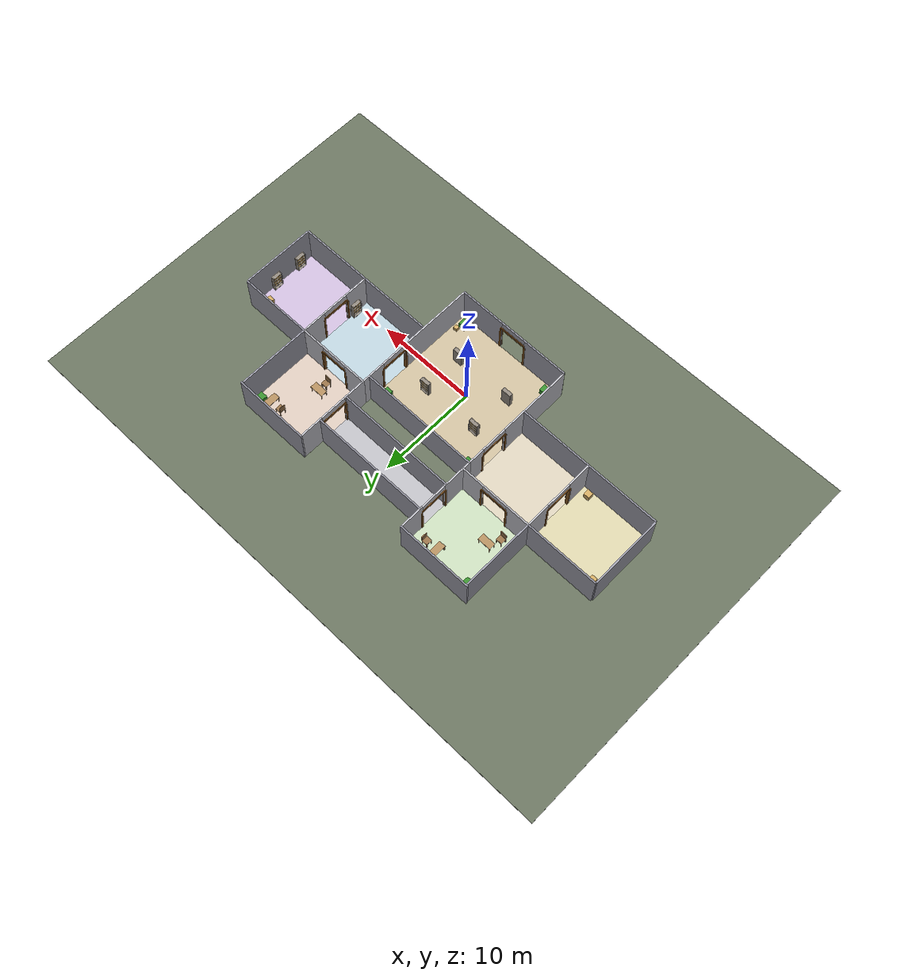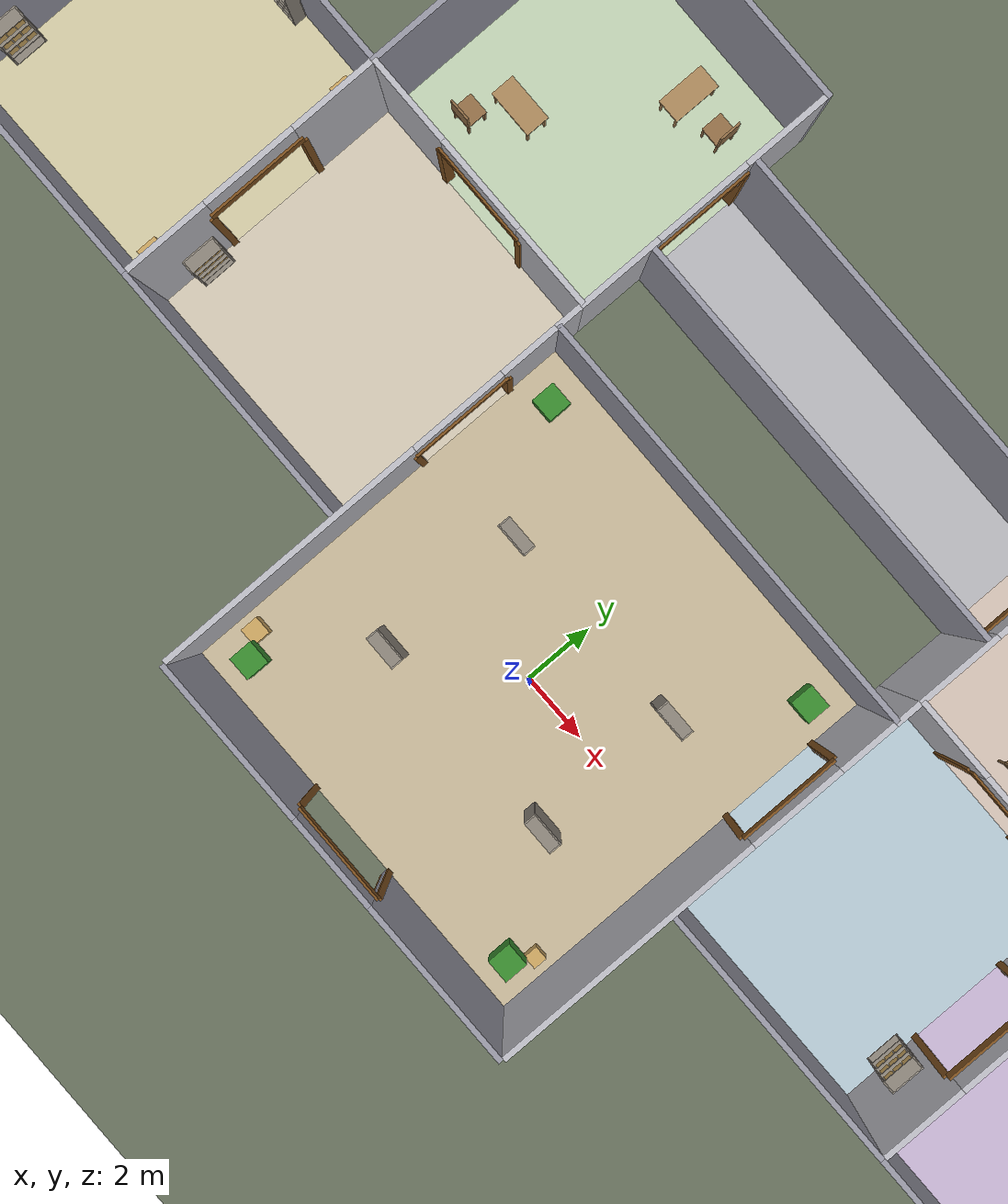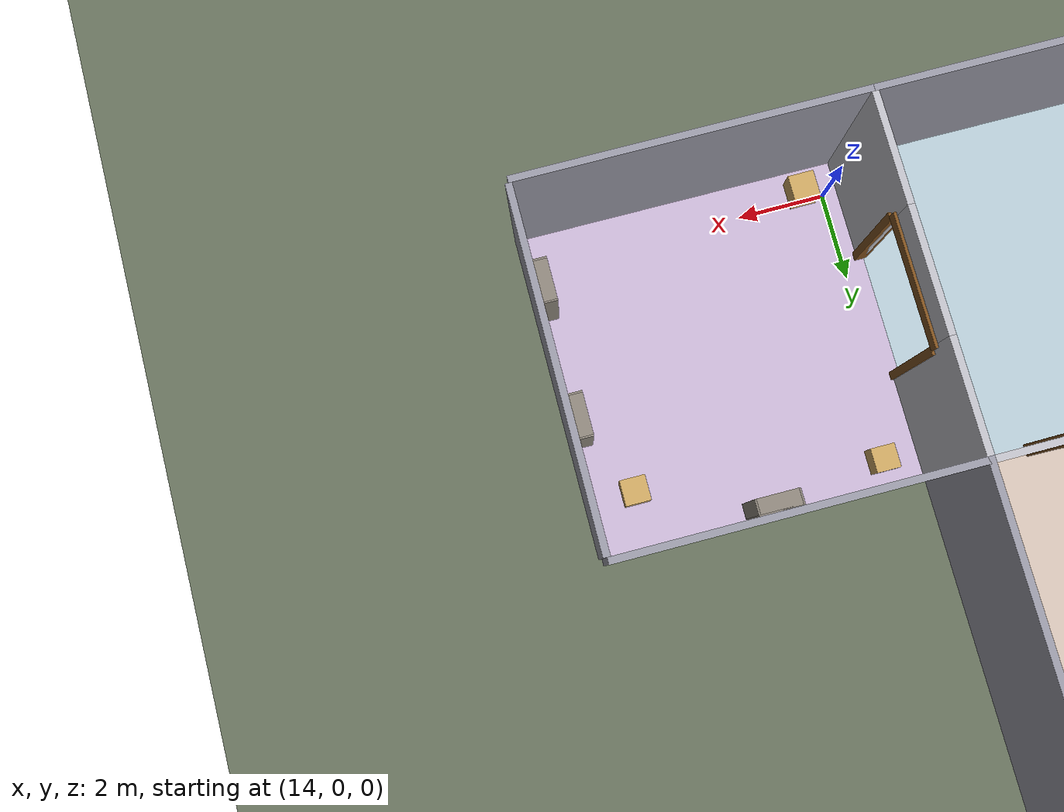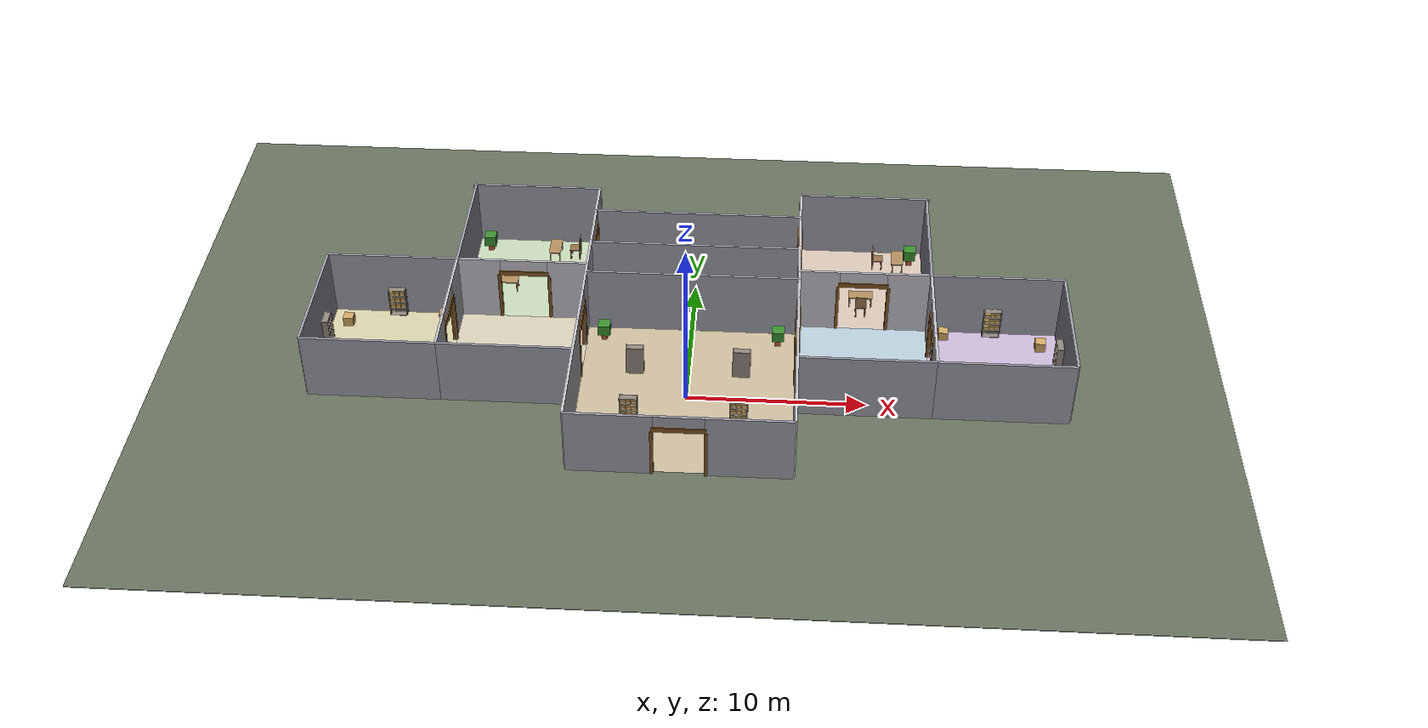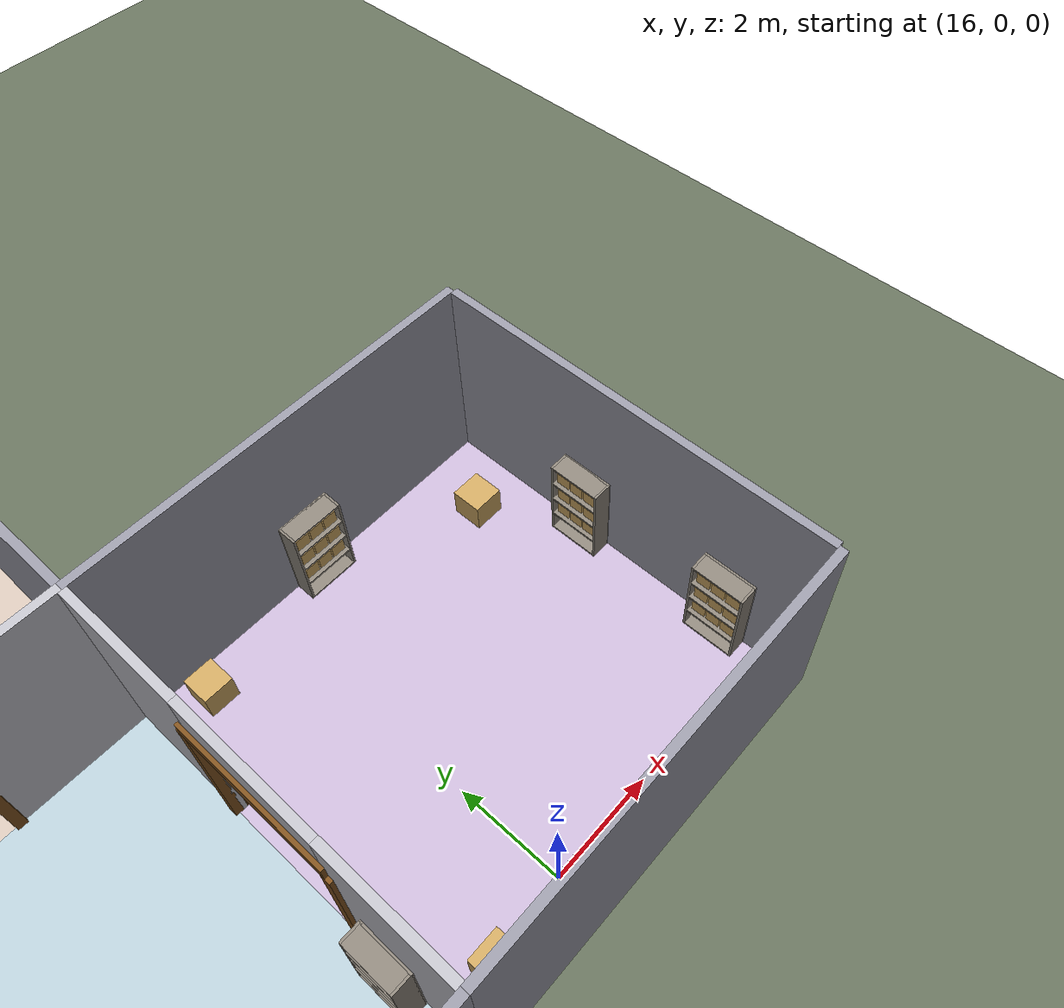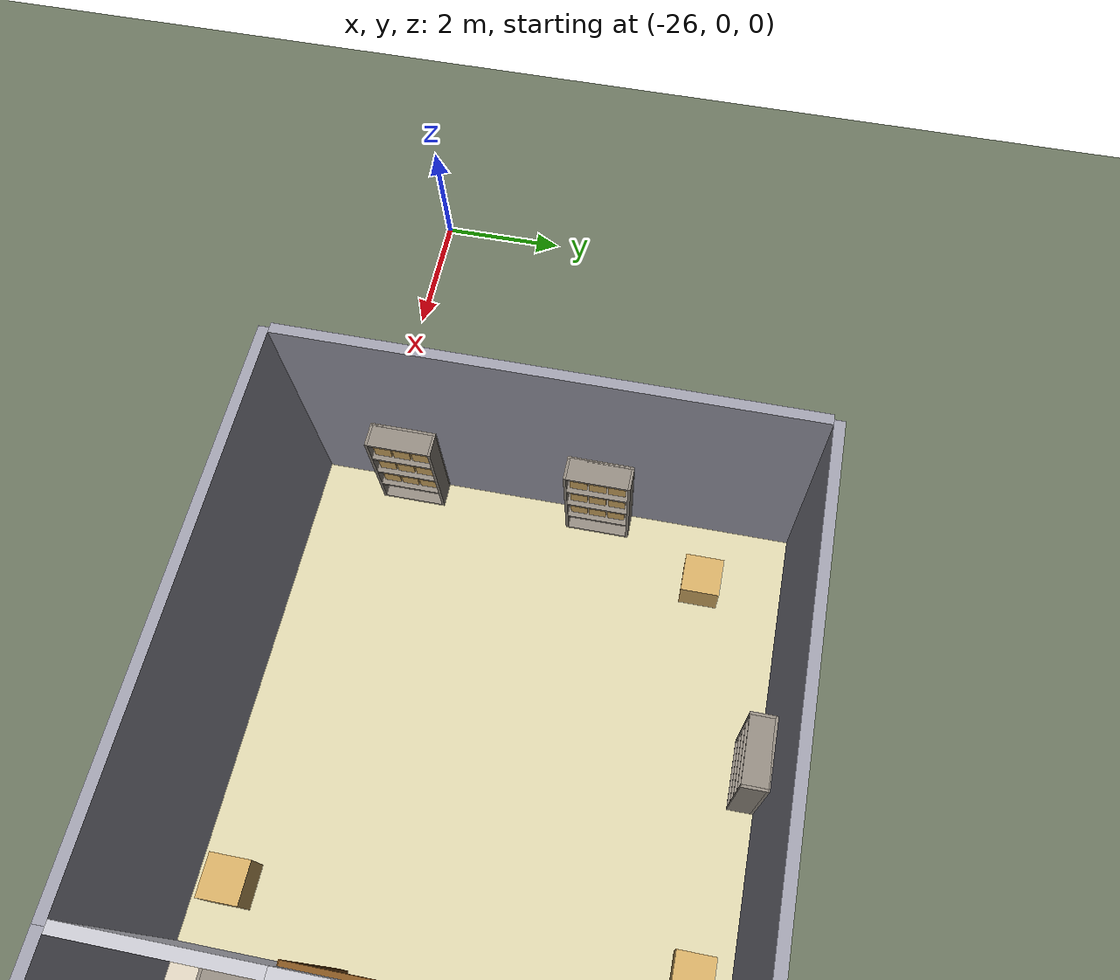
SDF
<?xml version="1.0"?>
<sdf version="1.8">
  <world name="indoor_rooms">

    <physics name="1ms" type="ignored">
      <max_step_size>0.001</max_step_size>
      <real_time_factor>1.0</real_time_factor>
    </physics>

    <plugin filename="gz-sim-physics-system"       name="gz::sim::systems::Physics"/>
    <plugin filename="gz-sim-user-commands-system" name="gz::sim::systems::UserCommands"/>
    <plugin filename="gz-sim-scene-broadcaster-system" name="gz::sim::systems::SceneBroadcaster"/>
    <plugin filename="gz-sim-sensors-system" name="gz::sim::systems::Sensors">
      <render_engine>ogre2</render_engine>
    </plugin>
    <plugin filename="gz-sim-imu-system" name="gz::sim::systems::Imu"/>

    <gui fullscreen="0">
      <plugin filename="MinimalScene" name="3D View">
        <gz-gui>
          <title>3D View</title>
          <property type="bool" key="showTitleBar">false</property>
          <property type="string" key="state">docked</property>
        </gz-gui>
        <engine>ogre2</engine>
        <scene>scene</scene>
        <ambient_light>0.5 0.5 0.5</ambient_light>
        <background_color>0.65 0.75 0.90</background_color>
        <camera_pose>0 -28 32 0 0.85 1.5708</camera_pose>
        <camera_clip><near>0.25</near><far>2000</far></camera_clip>
        <camera_clip><near>0.25</near><far>500</far></camera_clip>
      </plugin>
      <plugin filename="GzSceneManager" name="Scene Manager">
        <gz-gui>
          <property key="resizable" type="bool">false</property>
          <property key="width" type="double">5</property>
          <property key="height" type="double">5</property>
          <property key="state" type="string">floating</property>
          <property key="showTitleBar" type="bool">false</property>
        </gz-gui>
      </plugin>
      <plugin filename="EntityContextMenuPlugin" name="Entity context menu">
        <gz-gui>
          <property key="state" type="string">floating</property>
          <property key="width" type="double">5</property>
          <property key="height" type="double">5</property>
          <property key="showTitleBar" type="bool">false</property>
        </gz-gui>
      </plugin>
      <plugin filename="WorldControl" name="World control">
        <gz-gui>
          <title>World control</title>
          <property type="bool" key="showTitleBar">false</property>
          <property type="bool" key="resizable">false</property>
          <property type="double" key="height">72</property>
          <property type="double" key="width">121</property>
          <property type="double" key="z">1</property>
          <property type="string" key="state">floating</property>
          <anchors target="3D View">
            <line own="left" target="left"/>
            <line own="bottom" target="bottom"/>
          </anchors>
        </gz-gui>
        <play_pause>true</play_pause>
        <step>true</step>
        <start_paused>true</start_paused>
        <service>/world/indoor_rooms/control</service>
        <stats_topic>/world/indoor_rooms/stats</stats_topic>
      </plugin>
      <plugin filename="WorldStats" name="World stats">
        <gz-gui>
          <title>World stats</title>
          <property type="bool" key="showTitleBar">false</property>
          <property type="bool" key="resizable">false</property>
          <property type="double" key="height">110</property>
          <property type="double" key="width">290</property>
          <property type="double" key="z">1</property>
          <property type="string" key="state">floating</property>
          <anchors target="3D View">
            <line own="right" target="right"/>
            <line own="bottom" target="bottom"/>
          </anchors>
        </gz-gui>
        <sim_time>true</sim_time>
        <real_time>true</real_time>
        <real_time_factor>true</real_time_factor>
        <iterations>true</iterations>
        <topic>/world/indoor_rooms/stats</topic>
      </plugin>
      <plugin filename="TransformControl" name="Transform control">
        <gz-gui>
          <property key="resizable" type="bool">false</property>
          <property key="width" type="double">250</property>
          <property key="height" type="double">50</property>
          <property key="state" type="string">floating</property>
          <property key="showTitleBar" type="bool">false</property>
          <anchors target="3D View">
            <line own="left" target="left"/>
            <line own="top" target="top"/>
          </anchors>
        </gz-gui>
      </plugin>
      <plugin filename="Shapes" name="Shapes">
        <gz-gui>
          <property key="resizable" type="bool">false</property>
          <property key="width" type="double">300</property>
          <property key="height" type="double">50</property>
          <property key="state" type="string">floating</property>
          <property key="showTitleBar" type="bool">false</property>
        </gz-gui>
      </plugin>
      <plugin filename="Spawn" name="Spawn Entities">
        <gz-gui>
          <property key="resizable" type="bool">false</property>
          <property key="width" type="double">5</property>
          <property key="height" type="double">5</property>
          <property key="state" type="string">floating</property>
          <property key="showTitleBar" type="bool">false</property>
        </gz-gui>
      </plugin>
      <plugin filename="EntityTree" name="Entity tree"/>
      <plugin filename="InteractiveViewControl" name="Interactive view control"/>
    </gui>

    <light name="sun" type="directional">
      <pose>0 0 100 0 0 0</pose>
      <diffuse>0.85 0.85 0.85 1</diffuse>
      <specular>0.2 0.2 0.2 1</specular>
      <direction>0.3 0.3 -1</direction>
      <cast_shadows>false</cast_shadows>
    </light>

    <light name="light_a" type="point">
      <pose>0 0 2.8 0 0 0</pose>
      <diffuse>1 0.98 0.88 1</diffuse>
      <specular>0.1 0.1 0.1 1</specular>
      <attenuation><range>15</range><constant>0.3</constant><linear>0.04</linear><quadratic>0.005</quadratic></attenuation>
      <cast_shadows>false</cast_shadows>
    </light>
    <light name="light_b" type="point">
      <pose>-6.5 2.0 2.8 0 0 0</pose>
      <diffuse>1 0.98 0.88 1</diffuse>
      <specular>0.1 0.1 0.1 1</specular>
      <attenuation><range>10</range><constant>0.35</constant><linear>0.05</linear><quadratic>0.008</quadratic></attenuation>
      <cast_shadows>false</cast_shadows>
    </light>
    <light name="light_c" type="point">
      <pose>6.5 2.0 2.8 0 0 0</pose>
      <diffuse>1 0.98 0.88 1</diffuse>
      <specular>0.1 0.1 0.1 1</specular>
      <attenuation><range>10</range><constant>0.35</constant><linear>0.05</linear><quadratic>0.008</quadratic></attenuation>
      <cast_shadows>false</cast_shadows>
    </light>
    <light name="light_d" type="point">
      <pose>-6.5 7.0 2.8 0 0 0</pose>
      <diffuse>1 0.98 0.88 1</diffuse>
      <specular>0.1 0.1 0.1 1</specular>
      <attenuation><range>10</range><constant>0.35</constant><linear>0.05</linear><quadratic>0.008</quadratic></attenuation>
      <cast_shadows>false</cast_shadows>
    </light>
    <light name="light_e" type="point">
      <pose>6.5 7.0 2.8 0 0 0</pose>
      <diffuse>1 0.98 0.88 1</diffuse>
      <specular>0.1 0.1 0.1 1</specular>
      <attenuation><range>10</range><constant>0.35</constant><linear>0.05</linear><quadratic>0.008</quadratic></attenuation>
      <cast_shadows>false</cast_shadows>
    </light>
    <light name="light_f" type="point">
      <pose>11.5 2.0 2.8 0 0 0</pose>
      <diffuse>1 0.98 0.88 1</diffuse>
      <specular>0.1 0.1 0.1 1</specular>
      <attenuation><range>10</range><constant>0.35</constant><linear>0.05</linear><quadratic>0.008</quadratic></attenuation>
      <cast_shadows>false</cast_shadows>
    </light>
    <light name="light_g" type="point">
      <pose>-11.5 2.0 2.8 0 0 0</pose>
      <diffuse>1 0.98 0.88 1</diffuse>
      <specular>0.1 0.1 0.1 1</specular>
      <attenuation><range>10</range><constant>0.35</constant><linear>0.05</linear><quadratic>0.008</quadratic></attenuation>
      <cast_shadows>false</cast_shadows>
    </light>
    <light name="light_cor" type="point">
      <pose>0 7.0 2.8 0 0 0</pose>
      <diffuse>1 0.98 0.88 1</diffuse>
      <specular>0.1 0.1 0.1 1</specular>
      <attenuation><range>12</range><constant>0.4</constant><linear>0.06</linear><quadratic>0.01</quadratic></attenuation>
      <cast_shadows>false</cast_shadows>
    </light>

    <include>
      <name>building_ground</name>
      <uri>model://building_ground</uri>
      <pose>0 0 0 0 0 0</pose>
    </include>
    <include>
      <name>room_a</name>
      <uri>model://room_a</uri>
      <pose>0 0 0 0 0 0</pose>
    </include>
    <include>
      <name>room_b</name>
      <uri>model://room_b</uri>
      <pose>0 0 0 0 0 0</pose>
    </include>
    <include>
      <name>room_c</name>
      <uri>model://room_c</uri>
      <pose>0 0 0 0 0 0</pose>
    </include>
    <include>
      <name>room_d</name>
      <uri>model://room_d</uri>
      <pose>0 0 0 0 0 0</pose>
    </include>
    <include>
      <name>room_e</name>
      <uri>model://room_e</uri>
      <pose>0 0 0 0 0 0</pose>
    </include>
    <include>
      <name>room_f</name>
      <uri>model://room_f</uri>
      <pose>0 0 0 0 0 0</pose>
    </include>
    <include>
      <name>room_g</name>
      <uri>model://room_g</uri>
      <pose>0 0 0 0 0 0</pose>
    </include>
    <include>
      <name>room_corridor</name>
      <uri>model://room_corridor</uri>
      <pose>0 0 0 0 0 0</pose>
    </include>

  </world>
</sdf>

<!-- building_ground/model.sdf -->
<sdf version="1.8">
  <model name="building_ground">
    <static>true</static>
    <pose>0 0 0 0 0 0</pose>
    <link name="ground">
      <pose>0 4 -0.025 0 0 0</pose>
      <collision name="col"><geometry><box><size>60 40 0.05</size></box></geometry></collision>
      <visual name="vis">
        <geometry><box><size>60 40 0.05</size></box></geometry>
        <material><ambient>0.4 0.44 0.36 1</ambient><diffuse>0.4 0.44 0.36 1</diffuse></material>
      </visual>
    </link>
  </model>
</sdf>

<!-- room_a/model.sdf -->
<sdf version="1.8">
  <model name="room_a">
    <static>true</static>
    <pose>0 0 0 0 0 0</pose>
    <link name="floor_a">
      <pose>0.0 0.0 0.002 0 0 0</pose>
      <visual name="vis">
        <geometry><box><size>12.0 12.0 0.004</size></box></geometry>
        <material><ambient>0.78 0.72 0.6 1</ambient><diffuse>0.78 0.72 0.6 1</diffuse></material>
      </visual>
    </link>
    <link name="wall_a_s_l">
      <pose>-3.7125000000000004 -6.075 2.0 0 0 0</pose>
      <collision name="col"><geometry><box><size>4.725 0.15 4.0</size></box></geometry></collision>
      <visual name="vis">
        <geometry><box><size>4.725 0.15 4.0</size></box></geometry>
        <material><ambient>0.6 0.6 0.65 1</ambient><diffuse>0.6 0.6 0.65 1</diffuse></material>
      </visual>
    </link>
    <link name="wall_a_s_r">
      <pose>3.7125000000000004 -6.075 2.0 0 0 0</pose>
      <collision name="col"><geometry><box><size>4.725 0.15 4.0</size></box></geometry></collision>
      <visual name="vis">
        <geometry><box><size>4.725 0.15 4.0</size></box></geometry>
        <material><ambient>0.6 0.6 0.65 1</ambient><diffuse>0.6 0.6 0.65 1</diffuse></material>
      </visual>
    </link>
    <link name="wall_a_s_top">
      <pose>0.0 -6.075 3.5 0 0 0</pose>
      <collision name="col"><geometry><box><size>2.7 0.15 1.0</size></box></geometry></collision>
      <visual name="vis">
        <geometry><box><size>2.7 0.15 1.0</size></box></geometry>
        <material><ambient>0.6 0.6 0.65 1</ambient><diffuse>0.6 0.6 0.65 1</diffuse></material>
      </visual>
    </link>
    <link name="frm_entry_l">
      <pose>-1.4400000000000002 -6.075 1.5 0 0 0</pose>
      <visual name="vis">
        <geometry><box><size>0.18 0.28 3.0</size></box></geometry>
        <material><ambient>0.5 0.32 0.12 1</ambient><diffuse>0.5 0.32 0.12 1</diffuse></material>
      </visual>
    </link>
    <link name="frm_entry_r">
      <pose>1.4400000000000002 -6.075 1.5 0 0 0</pose>
      <visual name="vis">
        <geometry><box><size>0.18 0.28 3.0</size></box></geometry>
        <material><ambient>0.5 0.32 0.12 1</ambient><diffuse>0.5 0.32 0.12 1</diffuse></material>
      </visual>
    </link>
    <link name="frm_entry_t">
      <pose>0.0 -6.075 3.15 0 0 0</pose>
      <visual name="vis">
        <geometry><box><size>2.8800000000000003 0.28 0.3</size></box></geometry>
        <material><ambient>0.5 0.32 0.12 1</ambient><diffuse>0.5 0.32 0.12 1</diffuse></material>
      </visual>
    </link>
    <link name="wall_a_n">
      <pose>0.0 6.075 2.0 0 0 0</pose>
      <collision name="col"><geometry><box><size>12.15 0.15 4.0</size></box></geometry></collision>
      <visual name="vis">
        <geometry><box><size>12.15 0.15 4.0</size></box></geometry>
        <material><ambient>0.6 0.6 0.65 1</ambient><diffuse>0.6 0.6 0.65 1</diffuse></material>
      </visual>
    </link>
    <link name="wall_a_w_bot">
      <pose>-6.075 -2.175 2.0 0 0 0</pose>
      <collision name="col"><geometry><box><size>0.15 7.65 4.0</size></box></geometry></collision>
      <visual name="vis">
        <geometry><box><size>0.15 7.65 4.0</size></box></geometry>
        <material><ambient>0.75 0.75 0.78 1</ambient><diffuse>0.75 0.75 0.78 1</diffuse></material>
      </visual>
    </link>
    <link name="wall_a_w_top">
      <pose>-6.075 5.175 2.0 0 0 0</pose>
      <collision name="col"><geometry><box><size>0.15 1.6500000000000004 4.0</size></box></geometry></collision>
      <visual name="vis">
        <geometry><box><size>0.15 1.6500000000000004 4.0</size></box></geometry>
        <material><ambient>0.75 0.75 0.78 1</ambient><diffuse>0.75 0.75 0.78 1</diffuse></material>
      </visual>
    </link>
    <link name="wall_a_w_door_top">
      <pose>-6.075 3.0 3.5 0 0 0</pose>
      <collision name="col"><geometry><box><size>0.15 2.7 1.0</size></box></geometry></collision>
      <visual name="vis">
        <geometry><box><size>0.15 2.7 1.0</size></box></geometry>
        <material><ambient>0.75 0.75 0.78 1</ambient><diffuse>0.75 0.75 0.78 1</diffuse></material>
      </visual>
    </link>
    <link name="frm_ab_l">
      <pose>-6.075 1.5599999999999998 1.5 0 0 0</pose>
      <visual name="vis">
        <geometry><box><size>0.28 0.18 3.0</size></box></geometry>
        <material><ambient>0.5 0.32 0.12 1</ambient><diffuse>0.5 0.32 0.12 1</diffuse></material>
      </visual>
    </link>
    <link name="frm_ab_r">
      <pose>-6.075 4.44 1.5 0 0 0</pose>
      <visual name="vis">
        <geometry><box><size>0.28 0.18 3.0</size></box></geometry>
        <material><ambient>0.5 0.32 0.12 1</ambient><diffuse>0.5 0.32 0.12 1</diffuse></material>
      </visual>
    </link>
    <link name="frm_ab_t">
      <pose>-6.075 3.0 3.15 0 0 0</pose>
      <visual name="vis">
        <geometry><box><size>0.28 2.8800000000000003 0.3</size></box></geometry>
        <material><ambient>0.5 0.32 0.12 1</ambient><diffuse>0.5 0.32 0.12 1</diffuse></material>
      </visual>
    </link>
    <link name="wall_a_e_bot">
      <pose>6.075 -2.175 2.0 0 0 0</pose>
      <collision name="col"><geometry><box><size>0.15 7.65 4.0</size></box></geometry></collision>
      <visual name="vis">
        <geometry><box><size>0.15 7.65 4.0</size></box></geometry>
        <material><ambient>0.75 0.75 0.78 1</ambient><diffuse>0.75 0.75 0.78 1</diffuse></material>
      </visual>
    </link>
    <link name="wall_a_e_top">
      <pose>6.075 5.175 2.0 0 0 0</pose>
      <collision name="col"><geometry><box><size>0.15 1.6500000000000004 4.0</size></box></geometry></collision>
      <visual name="vis">
        <geometry><box><size>0.15 1.6500000000000004 4.0</size></box></geometry>
        <material><ambient>0.75 0.75 0.78 1</ambient><diffuse>0.75 0.75 0.78 1</diffuse></material>
      </visual>
    </link>
    <link name="wall_a_e_door_top">
      <pose>6.075 3.0 3.5 0 0 0</pose>
      <collision name="col"><geometry><box><size>0.15 2.7 1.0</size></box></geometry></collision>
      <visual name="vis">
        <geometry><box><size>0.15 2.7 1.0</size></box></geometry>
        <material><ambient>0.75 0.75 0.78 1</ambient><diffuse>0.75 0.75 0.78 1</diffuse></material>
      </visual>
    </link>
    <link name="frm_ac_l">
      <pose>6.075 1.5599999999999998 1.5 0 0 0</pose>
      <visual name="vis">
        <geometry><box><size>0.28 0.18 3.0</size></box></geometry>
        <material><ambient>0.5 0.32 0.12 1</ambient><diffuse>0.5 0.32 0.12 1</diffuse></material>
      </visual>
    </link>
    <link name="frm_ac_r">
      <pose>6.075 4.44 1.5 0 0 0</pose>
      <visual name="vis">
        <geometry><box><size>0.28 0.18 3.0</size></box></geometry>
        <material><ambient>0.5 0.32 0.12 1</ambient><diffuse>0.5 0.32 0.12 1</diffuse></material>
      </visual>
    </link>
    <link name="frm_ac_t">
      <pose>6.075 3.0 3.15 0 0 0</pose>
      <visual name="vis">
        <geometry><box><size>0.28 2.8800000000000003 0.3</size></box></geometry>
        <material><ambient>0.5 0.32 0.12 1</ambient><diffuse>0.5 0.32 0.12 1</diffuse></material>
      </visual>
    </link>
    <link name="shelf_a_r1a_back">
      <pose>-3.0 -1.97 0.9 0 0 0</pose>
      <collision name="col"><geometry><box><size>1.0 0.04 1.8</size></box></geometry></collision>
      <visual name="vis">
        <geometry><box><size>1.0 0.04 1.8</size></box></geometry>
        <material><ambient>0.55 0.52 0.48 1</ambient><diffuse>0.55 0.52 0.48 1</diffuse></material>
      </visual>
    </link>
    <link name="shelf_a_r1a_sl">
      <pose>-3.48 -2.15 0.9 0 0 0</pose>
      <collision name="col"><geometry><box><size>0.04 0.36000000000000004 1.8</size></box></geometry></collision>
      <visual name="vis">
        <geometry><box><size>0.04 0.36000000000000004 1.8</size></box></geometry>
        <material><ambient>0.55 0.52 0.48 1</ambient><diffuse>0.55 0.52 0.48 1</diffuse></material>
      </visual>
    </link>
    <link name="shelf_a_r1a_sr">
      <pose>-2.52 -2.15 0.9 0 0 0</pose>
      <collision name="col"><geometry><box><size>0.04 0.36000000000000004 1.8</size></box></geometry></collision>
      <visual name="vis">
        <geometry><box><size>0.04 0.36000000000000004 1.8</size></box></geometry>
        <material><ambient>0.55 0.52 0.48 1</ambient><diffuse>0.55 0.52 0.48 1</diffuse></material>
      </visual>
    </link>
    <link name="shelf_a_r1a_brd0">
      <pose>-3.0 -2.15 0.02 0 0 0</pose>
      <collision name="col"><geometry><box><size>0.92 0.36000000000000004 0.04</size></box></geometry></collision>
      <visual name="vis">
        <geometry><box><size>0.92 0.36000000000000004 0.04</size></box></geometry>
        <material><ambient>0.55 0.52 0.48 1</ambient><diffuse>0.55 0.52 0.48 1</diffuse></material>
      </visual>
    </link>
    <link name="shelf_a_r1a_brd1">
      <pose>-3.0 -2.15 0.46 0 0 0</pose>
      <collision name="col"><geometry><box><size>0.92 0.36000000000000004 0.04</size></box></geometry></collision>
      <visual name="vis">
        <geometry><box><size>0.92 0.36000000000000004 0.04</size></box></geometry>
        <material><ambient>0.55 0.52 0.48 1</ambient><diffuse>0.55 0.52 0.48 1</diffuse></material>
      </visual>
    </link>
    <link name="shelf_a_r1a_brd2">
      <pose>-3.0 -2.15 0.9 0 0 0</pose>
      <collision name="col"><geometry><box><size>0.92 0.36000000000000004 0.04</size></box></geometry></collision>
      <visual name="vis">
        <geometry><box><size>0.92 0.36000000000000004 0.04</size></box></geometry>
        <material><ambient>0.55 0.52 0.48 1</ambient><diffuse>0.55 0.52 0.48 1</diffuse></material>
      </visual>
    </link>
    <link name="shelf_a_r1a_brd3">
      <pose>-3.0 -2.15 1.34 0 0 0</pose>
      <collision name="col"><geometry><box><size>0.92 0.36000000000000004 0.04</size></box></geometry></collision>
      <visual name="vis">
        <geometry><box><size>0.92 0.36000000000000004 0.04</size></box></geometry>
        <material><ambient>0.55 0.52 0.48 1</ambient><diffuse>0.55 0.52 0.48 1</diffuse></material>
      </visual>
    </link>
    <link name="shelf_a_r1a_brd4">
      <pose>-3.0 -2.15 1.78 0 0 0</pose>
      <collision name="col"><geometry><box><size>0.92 0.36000000000000004 0.04</size></box></geometry></collision>
      <visual name="vis">
        <geometry><box><size>0.92 0.36000000000000004 0.04</size></box></geometry>
        <material><ambient>0.55 0.52 0.48 1</ambient><diffuse>0.55 0.52 0.48 1</diffuse></material>
      </visual>
    </link>
    <link name="shelf_a_r1a_bx10">
      <pose>-3.29 -2.12 0.61 0 0 0</pose>
      <collision name="col"><geometry><box><size>0.26 0.26 0.26</size></box></geometry></collision>
      <visual name="vis">
        <geometry><box><size>0.26 0.26 0.26</size></box></geometry>
        <material><ambient>0.8 0.65 0.38 1</ambient><diffuse>0.8 0.65 0.38 1</diffuse></material>
      </visual>
    </link>
    <link name="shelf_a_r1a_bx11">
      <pose>-3.0 -2.12 0.61 0 0 0</pose>
      <collision name="col"><geometry><box><size>0.26 0.26 0.26</size></box></geometry></collision>
      <visual name="vis">
        <geometry><box><size>0.26 0.26 0.26</size></box></geometry>
        <material><ambient>0.8 0.65 0.38 1</ambient><diffuse>0.8 0.65 0.38 1</diffuse></material>
      </visual>
    </link>
    <link name="shelf_a_r1a_bx12">
      <pose>-2.71 -2.12 0.61 0 0 0</pose>
      <collision name="col"><geometry><box><size>0.26 0.26 0.26</size></box></geometry></collision>
      <visual name="vis">
        <geometry><box><size>0.26 0.26 0.26</size></box></geometry>
        <material><ambient>0.8 0.65 0.38 1</ambient><diffuse>0.8 0.65 0.38 1</diffuse></material>
      </visual>
    </link>
    <link name="shelf_a_r1a_bx20">
      <pose>-3.29 -2.12 1.05 0 0 0</pose>
      <collision name="col"><geometry><box><size>0.26 0.26 0.26</size></box></geometry></collision>
      <visual name="vis">
        <geometry><box><size>0.26 0.26 0.26</size></box></geometry>
        <material><ambient>0.8 0.65 0.38 1</ambient><diffuse>0.8 0.65 0.38 1</diffuse></material>
      </visual>
    </link>
    <link name="shelf_a_r1a_bx21">
      <pose>-3.0 -2.12 1.05 0 0 0</pose>
      <collision name="col"><geometry><box><size>0.26 0.26 0.26</size></box></geometry></collision>
      <visual name="vis">
        <geometry><box><size>0.26 0.26 0.26</size></box></geometry>
        <material><ambient>0.8 0.65 0.38 1</ambient><diffuse>0.8 0.65 0.38 1</diffuse></material>
      </visual>
    </link>
    <link name="shelf_a_r1a_bx22">
      <pose>-2.71 -2.12 1.05 0 0 0</pose>
      <collision name="col"><geometry><box><size>0.26 0.26 0.26</size></box></geometry></collision>
      <visual name="vis">
        <geometry><box><size>0.26 0.26 0.26</size></box></geometry>
        <material><ambient>0.8 0.65 0.38 1</ambient><diffuse>0.8 0.65 0.38 1</diffuse></material>
      </visual>
    </link>
    <link name="shelf_a_r1a_bx30">
      <pose>-3.29 -2.12 1.4900000000000002 0 0 0</pose>
      <collision name="col"><geometry><box><size>0.26 0.26 0.26</size></box></geometry></collision>
      <visual name="vis">
        <geometry><box><size>0.26 0.26 0.26</size></box></geometry>
        <material><ambient>0.8 0.65 0.38 1</ambient><diffuse>0.8 0.65 0.38 1</diffuse></material>
      </visual>
    </link>
    <link name="shelf_a_r1a_bx31">
      <pose>-3.0 -2.12 1.4900000000000002 0 0 0</pose>
      <collision name="col"><geometry><box><size>0.26 0.26 0.26</size></box></geometry></collision>
      <visual name="vis">
        <geometry><box><size>0.26 0.26 0.26</size></box></geometry>
        <material><ambient>0.8 0.65 0.38 1</ambient><diffuse>0.8 0.65 0.38 1</diffuse></material>
      </visual>
    </link>
    <link name="shelf_a_r1a_bx32">
      <pose>-2.71 -2.12 1.4900000000000002 0 0 0</pose>
      <collision name="col"><geometry><box><size>0.26 0.26 0.26</size></box></geometry></collision>
      <visual name="vis">
        <geometry><box><size>0.26 0.26 0.26</size></box></geometry>
        <material><ambient>0.8 0.65 0.38 1</ambient><diffuse>0.8 0.65 0.38 1</diffuse></material>
      </visual>
    </link>
    <link name="shelf_a_r1b_back">
      <pose>3.0 -1.97 0.9 0 0 0</pose>
      <collision name="col"><geometry><box><size>1.0 0.04 1.8</size></box></geometry></collision>
      <visual name="vis">
        <geometry><box><size>1.0 0.04 1.8</size></box></geometry>
        <material><ambient>0.55 0.52 0.48 1</ambient><diffuse>0.55 0.52 0.48 1</diffuse></material>
      </visual>
    </link>
    <link name="shelf_a_r1b_sl">
      <pose>2.52 -2.15 0.9 0 0 0</pose>
      <collision name="col"><geometry><box><size>0.04 0.36000000000000004 1.8</size></box></geometry></collision>
      <visual name="vis">
        <geometry><box><size>0.04 0.36000000000000004 1.8</size></box></geometry>
        <material><ambient>0.55 0.52 0.48 1</ambient><diffuse>0.55 0.52 0.48 1</diffuse></material>
      </visual>
    </link>
    <link name="shelf_a_r1b_sr">
      <pose>3.48 -2.15 0.9 0 0 0</pose>
      <collision name="col"><geometry><box><size>0.04 0.36000000000000004 1.8</size></box></geometry></collision>
      <visual name="vis">
        <geometry><box><size>0.04 0.36000000000000004 1.8</size></box></geometry>
        <material><ambient>0.55 0.52 0.48 1</ambient><diffuse>0.55 0.52 0.48 1</diffuse></material>
      </visual>
    </link>
    <link name="shelf_a_r1b_brd0">
      <pose>3.0 -2.15 0.02 0 0 0</pose>
      <collision name="col"><geometry><box><size>0.92 0.36000000000000004 0.04</size></box></geometry></collision>
      <visual name="vis">
        <geometry><box><size>0.92 0.36000000000000004 0.04</size></box></geometry>
        <material><ambient>0.55 0.52 0.48 1</ambient><diffuse>0.55 0.52 0.48 1</diffuse></material>
      </visual>
    </link>
    <link name="shelf_a_r1b_brd1">
      <pose>3.0 -2.15 0.46 0 0 0</pose>
      <collision name="col"><geometry><box><size>0.92 0.36000000000000004 0.04</size></box></geometry></collision>
      <visual name="vis">
        <geometry><box><size>0.92 0.36000000000000004 0.04</size></box></geometry>
        <material><ambient>0.55 0.52 0.48 1</ambient><diffuse>0.55 0.52 0.48 1</diffuse></material>
      </visual>
    </link>
    <link name="shelf_a_r1b_brd2">
      <pose>3.0 -2.15 0.9 0 0 0</pose>
      <collision name="col"><geometry><box><size>0.92 0.36000000000000004 0.04</size></box></geometry></collision>
      <visual name="vis">
        <geometry><box><size>0.92 0.36000000000000004 0.04</size></box></geometry>
        <material><ambient>0.55 0.52 0.48 1</ambient><diffuse>0.55 0.52 0.48 1</diffuse></material>
      </visual>
    </link>
    <link name="shelf_a_r1b_brd3">
      <pose>3.0 -2.15 1.34 0 0 0</pose>
      <collision name="col"><geometry><box><size>0.92 0.36000000000000004 0.04</size></box></geometry></collision>
      <visual name="vis">
        <geometry><box><size>0.92 0.36000000000000004 0.04</size></box></geometry>
        <material><ambient>0.55 0.52 0.48 1</ambient><diffuse>0.55 0.52 0.48 1</diffuse></material>
      </visual>
    </link>
    <link name="shelf_a_r1b_brd4">
      <pose>3.0 -2.15 1.78 0 0 0</pose>
      <collision name="col"><geometry><box><size>0.92 0.36000000000000004 0.04</size></box></geometry></collision>
      <visual name="vis">
        <geometry><box><size>0.92 0.36000000000000004 0.04</size></box></geometry>
        <material><ambient>0.55 0.52 0.48 1</ambient><diffuse>0.55 0.52 0.48 1</diffuse></material>
      </visual>
    </link>
    <link name="shelf_a_r1b_bx10">
      <pose>2.71 -2.12 0.61 0 0 0</pose>
      <collision name="col"><geometry><box><size>0.26 0.26 0.26</size></box></geometry></collision>
      <visual name="vis">
        <geometry><box><size>0.26 0.26 0.26</size></box></geometry>
        <material><ambient>0.8 0.65 0.38 1</ambient><diffuse>0.8 0.65 0.38 1</diffuse></material>
      </visual>
    </link>
    <link name="shelf_a_r1b_bx11">
      <pose>3.0 -2.12 0.61 0 0 0</pose>
      <collision name="col"><geometry><box><size>0.26 0.26 0.26</size></box></geometry></collision>
      <visual name="vis">
        <geometry><box><size>0.26 0.26 0.26</size></box></geometry>
        <material><ambient>0.8 0.65 0.38 1</ambient><diffuse>0.8 0.65 0.38 1</diffuse></material>
      </visual>
    </link>
    <link name="shelf_a_r1b_bx12">
      <pose>3.29 -2.12 0.61 0 0 0</pose>
      <collision name="col"><geometry><box><size>0.26 0.26 0.26</size></box></geometry></collision>
      <visual name="vis">
        <geometry><box><size>0.26 0.26 0.26</size></box></geometry>
        <material><ambient>0.8 0.65 0.38 1</ambient><diffuse>0.8 0.65 0.38 1</diffuse></material>
      </visual>
    </link>
    <link name="shelf_a_r1b_bx20">
      <pose>2.71 -2.12 1.05 0 0 0</pose>
      <collision name="col"><geometry><box><size>0.26 0.26 0.26</size></box></geometry></collision>
      <visual name="vis">
        <geometry><box><size>0.26 0.26 0.26</size></box></geometry>
        <material><ambient>0.8 0.65 0.38 1</ambient><diffuse>0.8 0.65 0.38 1</diffuse></material>
      </visual>
    </link>
    <link name="shelf_a_r1b_bx21">
      <pose>3.0 -2.12 1.05 0 0 0</pose>
      <collision name="col"><geometry><box><size>0.26 0.26 0.26</size></box></geometry></collision>
      <visual name="vis">
        <geometry><box><size>0.26 0.26 0.26</size></box></geometry>
        <material><ambient>0.8 0.65 0.38 1</ambient><diffuse>0.8 0.65 0.38 1</diffuse></material>
      </visual>
    </link>
    <link name="shelf_a_r1b_bx22">
      <pose>3.29 -2.12 1.05 0 0 0</pose>
      <collision name="col"><geometry><box><size>0.26 0.26 0.26</size></box></geometry></collision>
      <visual name="vis">
        <geometry><box><size>0.26 0.26 0.26</size></box></geometry>
        <material><ambient>0.8 0.65 0.38 1</ambient><diffuse>0.8 0.65 0.38 1</diffuse></material>
      </visual>
    </link>
    <link name="shelf_a_r1b_bx30">
      <pose>2.71 -2.12 1.4900000000000002 0 0 0</pose>
      <collision name="col"><geometry><box><size>0.26 0.26 0.26</size></box></geometry></collision>
      <visual name="vis">
        <geometry><box><size>0.26 0.26 0.26</size></box></geometry>
        <material><ambient>0.8 0.65 0.38 1</ambient><diffuse>0.8 0.65 0.38 1</diffuse></material>
      </visual>
    </link>
    <link name="shelf_a_r1b_bx31">
      <pose>3.0 -2.12 1.4900000000000002 0 0 0</pose>
      <collision name="col"><geometry><box><size>0.26 0.26 0.26</size></box></geometry></collision>
      <visual name="vis">
        <geometry><box><size>0.26 0.26 0.26</size></box></geometry>
        <material><ambient>0.8 0.65 0.38 1</ambient><diffuse>0.8 0.65 0.38 1</diffuse></material>
      </visual>
    </link>
    <link name="shelf_a_r1b_bx32">
      <pose>3.29 -2.12 1.4900000000000002 0 0 0</pose>
      <collision name="col"><geometry><box><size>0.26 0.26 0.26</size></box></geometry></collision>
      <visual name="vis">
        <geometry><box><size>0.26 0.26 0.26</size></box></geometry>
        <material><ambient>0.8 0.65 0.38 1</ambient><diffuse>0.8 0.65 0.38 1</diffuse></material>
      </visual>
    </link>
    <link name="shelf_a_r2a_back">
      <pose>-3.0 1.97 0.9 0 0 0</pose>
      <collision name="col"><geometry><box><size>1.0 0.04 1.8</size></box></geometry></collision>
      <visual name="vis">
        <geometry><box><size>1.0 0.04 1.8</size></box></geometry>
        <material><ambient>0.55 0.52 0.48 1</ambient><diffuse>0.55 0.52 0.48 1</diffuse></material>
      </visual>
    </link>
    <link name="shelf_a_r2a_sl">
      <pose>-3.48 2.15 0.9 0 0 0</pose>
      <collision name="col"><geometry><box><size>0.04 0.36000000000000004 1.8</size></box></geometry></collision>
      <visual name="vis">
        <geometry><box><size>0.04 0.36000000000000004 1.8</size></box></geometry>
        <material><ambient>0.55 0.52 0.48 1</ambient><diffuse>0.55 0.52 0.48 1</diffuse></material>
      </visual>
    </link>
    <link name="shelf_a_r2a_sr">
      <pose>-2.52 2.15 0.9 0 0 0</pose>
      <collision name="col"><geometry><box><size>0.04 0.36000000000000004 1.8</size></box></geometry></collision>
      <visual name="vis">
        <geometry><box><size>0.04 0.36000000000000004 1.8</size></box></geometry>
        <material><ambient>0.55 0.52 0.48 1</ambient><diffuse>0.55 0.52 0.48 1</diffuse></material>
      </visual>
    </link>
    <link name="shelf_a_r2a_brd0">
      <pose>-3.0 2.15 0.02 0 0 0</pose>
      <collision name="col"><geometry><box><size>0.92 0.36000000000000004 0.04</size></box></geometry></collision>
      <visual name="vis">
        <geometry><box><size>0.92 0.36000000000000004 0.04</size></box></geometry>
        <material><ambient>0.55 0.52 0.48 1</ambient><diffuse>0.55 0.52 0.48 1</diffuse></material>
      </visual>
    </link>
    <link name="shelf_a_r2a_brd1">
      <pose>-3.0 2.15 0.46 0 0 0</pose>
      <collision name="col"><geometry><box><size>0.92 0.36000000000000004 0.04</size></box></geometry></collision>
      <visual name="vis">
        <geometry><box><size>0.92 0.36000000000000004 0.04</size></box></geometry>
        <material><ambient>0.55 0.52 0.48 1</ambient><diffuse>0.55 0.52 0.48 1</diffuse></material>
      </visual>
    </link>
    <link name="shelf_a_r2a_brd2">
      <pose>-3.0 2.15 0.9 0 0 0</pose>
      <collision name="col"><geometry><box><size>0.92 0.36000000000000004 0.04</size></box></geometry></collision>
      <visual name="vis">
        <geometry><box><size>0.92 0.36000000000000004 0.04</size></box></geometry>
        <material><ambient>0.55 0.52 0.48 1</ambient><diffuse>0.55 0.52 0.48 1</diffuse></material>
      </visual>
    </link>
    <link name="shelf_a_r2a_brd3">
      <pose>-3.0 2.15 1.34 0 0 0</pose>
      <collision name="col"><geometry><box><size>0.92 0.36000000000000004 0.04</size></box></geometry></collision>
      <visual name="vis">
        <geometry><box><size>0.92 0.36000000000000004 0.04</size></box></geometry>
        <material><ambient>0.55 0.52 0.48 1</ambient><diffuse>0.55 0.52 0.48 1</diffuse></material>
      </visual>
    </link>
    <link name="shelf_a_r2a_brd4">
      <pose>-3.0 2.15 1.78 0 0 0</pose>
      <collision name="col"><geometry><box><size>0.92 0.36000000000000004 0.04</size></box></geometry></collision>
      <visual name="vis">
        <geometry><box><size>0.92 0.36000000000000004 0.04</size></box></geometry>
        <material><ambient>0.55 0.52 0.48 1</ambient><diffuse>0.55 0.52 0.48 1</diffuse></material>
      </visual>
    </link>
    <link name="shelf_a_r2a_bx10">
      <pose>-3.29 2.12 0.61 0 0 0</pose>
      <collision name="col"><geometry><box><size>0.26 0.26 0.26</size></box></geometry></collision>
      <visual name="vis">
        <geometry><box><size>0.26 0.26 0.26</size></box></geometry>
        <material><ambient>0.8 0.65 0.38 1</ambient><diffuse>0.8 0.65 0.38 1</diffuse></material>
      </visual>
    </link>
    <link name="shelf_a_r2a_bx11">
      <pose>-3.0 2.12 0.61 0 0 0</pose>
      <collision name="col"><geometry><box><size>0.26 0.26 0.26</size></box></geometry></collision>
      <visual name="vis">
        <geometry><box><size>0.26 0.26 0.26</size></box></geometry>
        <material><ambient>0.8 0.65 0.38 1</ambient><diffuse>0.8 0.65 0.38 1</diffuse></material>
      </visual>
    </link>
    <link name="shelf_a_r2a_bx12">
      <pose>-2.71 2.12 0.61 0 0 0</pose>
      <collision name="col"><geometry><box><size>0.26 0.26 0.26</size></box></geometry></collision>
      <visual name="vis">
        <geometry><box><size>0.26 0.26 0.26</size></box></geometry>
        <material><ambient>0.8 0.65 0.38 1</ambient><diffuse>0.8 0.65 0.38 1</diffuse></material>
      </visual>
    </link>
    <link name="shelf_a_r2a_bx20">
      <pose>-3.29 2.12 1.05 0 0 0</pose>
      <collision name="col"><geometry><box><size>0.26 0.26 0.26</size></box></geometry></collision>
      <visual name="vis">
        <geometry><box><size>0.26 0.26 0.26</size></box></geometry>
        <material><ambient>0.8 0.65 0.38 1</ambient><diffuse>0.8 0.65 0.38 1</diffuse></material>
      </visual>
    </link>
    <link name="shelf_a_r2a_bx21">
      <pose>-3.0 2.12 1.05 0 0 0</pose>
      <collision name="col"><geometry><box><size>0.26 0.26 0.26</size></box></geometry></collision>
      <visual name="vis">
        <geometry><box><size>0.26 0.26 0.26</size></box></geometry>
        <material><ambient>0.8 0.65 0.38 1</ambient><diffuse>0.8 0.65 0.38 1</diffuse></material>
      </visual>
    </link>
    <link name="shelf_a_r2a_bx22">
      <pose>-2.71 2.12 1.05 0 0 0</pose>
      <collision name="col"><geometry><box><size>0.26 0.26 0.26</size></box></geometry></collision>
      <visual name="vis">
        <geometry><box><size>0.26 0.26 0.26</size></box></geometry>
        <material><ambient>0.8 0.65 0.38 1</ambient><diffuse>0.8 0.65 0.38 1</diffuse></material>
      </visual>
    </link>
    <link name="shelf_a_r2a_bx30">
      <pose>-3.29 2.12 1.4900000000000002 0 0 0</pose>
      <collision name="col"><geometry><box><size>0.26 0.26 0.26</size></box></geometry></collision>
      <visual name="vis">
        <geometry><box><size>0.26 0.26 0.26</size></box></geometry>
        <material><ambient>0.8 0.65 0.38 1</ambient><diffuse>0.8 0.65 0.38 1</diffuse></material>
      </visual>
    </link>
    <link name="shelf_a_r2a_bx31">
      <pose>-3.0 2.12 1.4900000000000002 0 0 0</pose>
      <collision name="col"><geometry><box><size>0.26 0.26 0.26</size></box></geometry></collision>
      <visual name="vis">
        <geometry><box><size>0.26 0.26 0.26</size></box></geometry>
        <material><ambient>0.8 0.65 0.38 1</ambient><diffuse>0.8 0.65 0.38 1</diffuse></material>
      </visual>
    </link>
    <link name="shelf_a_r2a_bx32">
      <pose>-2.71 2.12 1.4900000000000002 0 0 0</pose>
      <collision name="col"><geometry><box><size>0.26 0.26 0.26</size></box></geometry></collision>
      <visual name="vis">
        <geometry><box><size>0.26 0.26 0.26</size></box></geometry>
        <material><ambient>0.8 0.65 0.38 1</ambient><diffuse>0.8 0.65 0.38 1</diffuse></material>
      </visual>
    </link>
    <link name="shelf_a_r2b_back">
      <pose>3.0 1.97 0.9 0 0 0</pose>
      <collision name="col"><geometry><box><size>1.0 0.04 1.8</size></box></geometry></collision>
      <visual name="vis">
        <geometry><box><size>1.0 0.04 1.8</size></box></geometry>
        <material><ambient>0.55 0.52 0.48 1</ambient><diffuse>0.55 0.52 0.48 1</diffuse></material>
      </visual>
    </link>
    <link name="shelf_a_r2b_sl">
      <pose>2.52 2.15 0.9 0 0 0</pose>
      <collision name="col"><geometry><box><size>0.04 0.36000000000000004 1.8</size></box></geometry></collision>
      <visual name="vis">
        <geometry><box><size>0.04 0.36000000000000004 1.8</size></box></geometry>
        <material><ambient>0.55 0.52 0.48 1</ambient><diffuse>0.55 0.52 0.48 1</diffuse></material>
      </visual>
    </link>
    <link name="shelf_a_r2b_sr">
      <pose>3.48 2.15 0.9 0 0 0</pose>
      <collision name="col"><geometry><box><size>0.04 0.36000000000000004 1.8</size></box></geometry></collision>
      <visual name="vis">
        <geometry><box><size>0.04 0.36000000000000004 1.8</size></box></geometry>
        <material><ambient>0.55 0.52 0.48 1</ambient><diffuse>0.55 0.52 0.48 1</diffuse></material>
      </visual>
    </link>
    <link name="shelf_a_r2b_brd0">
      <pose>3.0 2.15 0.02 0 0 0</pose>
      <collision name="col"><geometry><box><size>0.92 0.36000000000000004 0.04</size></box></geometry></collision>
      <visual name="vis">
        <geometry><box><size>0.92 0.36000000000000004 0.04</size></box></geometry>
        <material><ambient>0.55 0.52 0.48 1</ambient><diffuse>0.55 0.52 0.48 1</diffuse></material>
      </visual>
    </link>
    <link name="shelf_a_r2b_brd1">
      <pose>3.0 2.15 0.46 0 0 0</pose>
      <collision name="col"><geometry><box><size>0.92 0.36000000000000004 0.04</size></box></geometry></collision>
      <visual name="vis">
        <geometry><box><size>0.92 0.36000000000000004 0.04</size></box></geometry>
        <material><ambient>0.55 0.52 0.48 1</ambient><diffuse>0.55 0.52 0.48 1</diffuse></material>
      </visual>
    </link>
    <link name="shelf_a_r2b_brd2">
      <pose>3.0 2.15 0.9 0 0 0</pose>
      <collision name="col"><geometry><box><size>0.92 0.36000000000000004 0.04</size></box></geometry></collision>
      <visual name="vis">
        <geometry><box><size>0.92 0.36000000000000004 0.04</size></box></geometry>
        <material><ambient>0.55 0.52 0.48 1</ambient><diffuse>0.55 0.52 0.48 1</diffuse></material>
      </visual>
    </link>
    <link name="shelf_a_r2b_brd3">
      <pose>3.0 2.15 1.34 0 0 0</pose>
      <collision name="col"><geometry><box><size>0.92 0.36000000000000004 0.04</size></box></geometry></collision>
      <visual name="vis">
        <geometry><box><size>0.92 0.36000000000000004 0.04</size></box></geometry>
        <material><ambient>0.55 0.52 0.48 1</ambient><diffuse>0.55 0.52 0.48 1</diffuse></material>
      </visual>
    </link>
    <link name="shelf_a_r2b_brd4">
      <pose>3.0 2.15 1.78 0 0 0</pose>
      <collision name="col"><geometry><box><size>0.92 0.36000000000000004 0.04</size></box></geometry></collision>
      <visual name="vis">
        <geometry><box><size>0.92 0.36000000000000004 0.04</size></box></geometry>
        <material><ambient>0.55 0.52 0.48 1</ambient><diffuse>0.55 0.52 0.48 1</diffuse></material>
      </visual>
    </link>
    <link name="shelf_a_r2b_bx10">
      <pose>2.71 2.12 0.61 0 0 0</pose>
      <collision name="col"><geometry><box><size>0.26 0.26 0.26</size></box></geometry></collision>
      <visual name="vis">
        <geometry><box><size>0.26 0.26 0.26</size></box></geometry>
        <material><ambient>0.8 0.65 0.38 1</ambient><diffuse>0.8 0.65 0.38 1</diffuse></material>
      </visual>
    </link>
    <link name="shelf_a_r2b_bx11">
      <pose>3.0 2.12 0.61 0 0 0</pose>
      <collision name="col"><geometry><box><size>0.26 0.26 0.26</size></box></geometry></collision>
      <visual name="vis">
        <geometry><box><size>0.26 0.26 0.26</size></box></geometry>
        <material><ambient>0.8 0.65 0.38 1</ambient><diffuse>0.8 0.65 0.38 1</diffuse></material>
      </visual>
    </link>
    <link name="shelf_a_r2b_bx12">
      <pose>3.29 2.12 0.61 0 0 0</pose>
      <collision name="col"><geometry><box><size>0.26 0.26 0.26</size></box></geometry></collision>
      <visual name="vis">
        <geometry><box><size>0.26 0.26 0.26</size></box></geometry>
        <material><ambient>0.8 0.65 0.38 1</ambient><diffuse>0.8 0.65 0.38 1</diffuse></material>
      </visual>
    </link>
    <link name="shelf_a_r2b_bx20">
      <pose>2.71 2.12 1.05 0 0 0</pose>
      <collision name="col"><geometry><box><size>0.26 0.26 0.26</size></box></geometry></collision>
      <visual name="vis">
        <geometry><box><size>0.26 0.26 0.26</size></box></geometry>
        <material><ambient>0.8 0.65 0.38 1</ambient><diffuse>0.8 0.65 0.38 1</diffuse></material>
      </visual>
    </link>
    <link name="shelf_a_r2b_bx21">
      <pose>3.0 2.12 1.05 0 0 0</pose>
      <collision name="col"><geometry><box><size>0.26 0.26 0.26</size></box></geometry></collision>
      <visual name="vis">
        <geometry><box><size>0.26 0.26 0.26</size></box></geometry>
        <material><ambient>0.8 0.65 0.38 1</ambient><diffuse>0.8 0.65 0.38 1</diffuse></material>
      </visual>
    </link>
    <link name="shelf_a_r2b_bx22">
      <pose>3.29 2.12 1.05 0 0 0</pose>
      <collision name="col"><geometry><box><size>0.26 0.26 0.26</size></box></geometry></collision>
      <visual name="vis">
        <geometry><box><size>0.26 0.26 0.26</size></box></geometry>
        <material><ambient>0.8 0.65 0.38 1</ambient><diffuse>0.8 0.65 0.38 1</diffuse></material>
      </visual>
    </link>
    <link name="shelf_a_r2b_bx30">
      <pose>2.71 2.12 1.4900000000000002 0 0 0</pose>
      <collision name="col"><geometry><box><size>0.26 0.26 0.26</size></box></geometry></collision>
      <visual name="vis">
        <geometry><box><size>0.26 0.26 0.26</size></box></geometry>
        <material><ambient>0.8 0.65 0.38 1</ambient><diffuse>0.8 0.65 0.38 1</diffuse></material>
      </visual>
    </link>
    <link name="shelf_a_r2b_bx31">
      <pose>3.0 2.12 1.4900000000000002 0 0 0</pose>
      <collision name="col"><geometry><box><size>0.26 0.26 0.26</size></box></geometry></collision>
      <visual name="vis">
        <geometry><box><size>0.26 0.26 0.26</size></box></geometry>
        <material><ambient>0.8 0.65 0.38 1</ambient><diffuse>0.8 0.65 0.38 1</diffuse></material>
      </visual>
    </link>
    <link name="shelf_a_r2b_bx32">
      <pose>3.29 2.12 1.4900000000000002 0 0 0</pose>
      <collision name="col"><geometry><box><size>0.26 0.26 0.26</size></box></geometry></collision>
      <visual name="vis">
        <geometry><box><size>0.26 0.26 0.26</size></box></geometry>
        <material><ambient>0.8 0.65 0.38 1</ambient><diffuse>0.8 0.65 0.38 1</diffuse></material>
      </visual>
    </link>
    <link name="plant_a_sw_pot">
      <pose>-5.0 -5.0 0.225 0 0 0</pose>
      <collision name="col"><geometry><box><size>0.33 0.33 0.45</size></box></geometry></collision>
      <visual name="vis">
        <geometry><box><size>0.33 0.33 0.45</size></box></geometry>
        <material><ambient>0.72 0.35 0.2 1</ambient><diffuse>0.72 0.35 0.2 1</diffuse></material>
      </visual>
    </link>
    <link name="plant_a_sw_leaves">
      <pose>-5.0 -5.0 0.78 0 0 0</pose>
      <collision name="col"><geometry><box><size>0.69 0.69 0.66</size></box></geometry></collision>
      <visual name="vis">
        <geometry><box><size>0.69 0.69 0.66</size></box></geometry>
        <material><ambient>0.22 0.55 0.18 1</ambient><diffuse>0.22 0.55 0.18 1</diffuse></material>
      </visual>
    </link>
    <link name="plant_a_se_pot">
      <pose>5.0 -5.0 0.225 0 0 0</pose>
      <collision name="col"><geometry><box><size>0.33 0.33 0.45</size></box></geometry></collision>
      <visual name="vis">
        <geometry><box><size>0.33 0.33 0.45</size></box></geometry>
        <material><ambient>0.72 0.35 0.2 1</ambient><diffuse>0.72 0.35 0.2 1</diffuse></material>
      </visual>
    </link>
    <link name="plant_a_se_leaves">
      <pose>5.0 -5.0 0.78 0 0 0</pose>
      <collision name="col"><geometry><box><size>0.69 0.69 0.66</size></box></geometry></collision>
      <visual name="vis">
        <geometry><box><size>0.69 0.69 0.66</size></box></geometry>
        <material><ambient>0.22 0.55 0.18 1</ambient><diffuse>0.22 0.55 0.18 1</diffuse></material>
      </visual>
    </link>
    <link name="plant_a_nw_pot">
      <pose>-5.0 5.0 0.225 0 0 0</pose>
      <collision name="col"><geometry><box><size>0.33 0.33 0.45</size></box></geometry></collision>
      <visual name="vis">
        <geometry><box><size>0.33 0.33 0.45</size></box></geometry>
        <material><ambient>0.72 0.35 0.2 1</ambient><diffuse>0.72 0.35 0.2 1</diffuse></material>
      </visual>
    </link>
    <link name="plant_a_nw_leaves">
      <pose>-5.0 5.0 0.78 0 0 0</pose>
      <collision name="col"><geometry><box><size>0.69 0.69 0.66</size></box></geometry></collision>
      <visual name="vis">
        <geometry><box><size>0.69 0.69 0.66</size></box></geometry>
        <material><ambient>0.22 0.55 0.18 1</ambient><diffuse>0.22 0.55 0.18 1</diffuse></material>
      </visual>
    </link>
    <link name="plant_a_ne_pot">
      <pose>5.0 5.0 0.225 0 0 0</pose>
      <collision name="col"><geometry><box><size>0.33 0.33 0.45</size></box></geometry></collision>
      <visual name="vis">
        <geometry><box><size>0.33 0.33 0.45</size></box></geometry>
        <material><ambient>0.72 0.35 0.2 1</ambient><diffuse>0.72 0.35 0.2 1</diffuse></material>
      </visual>
    </link>
    <link name="plant_a_ne_leaves">
      <pose>5.0 5.0 0.78 0 0 0</pose>
      <collision name="col"><geometry><box><size>0.69 0.69 0.66</size></box></geometry></collision>
      <visual name="vis">
        <geometry><box><size>0.69 0.69 0.66</size></box></geometry>
        <material><ambient>0.22 0.55 0.18 1</ambient><diffuse>0.22 0.55 0.18 1</diffuse></material>
      </visual>
    </link>
    <link name="fbox_a1">
      <pose>5.5 -4.5 0.2 0 0 0</pose>
      <collision name="col"><geometry><box><size>0.4 0.4 0.4</size></box></geometry></collision>
      <visual name="vis">
        <geometry><box><size>0.4 0.4 0.4</size></box></geometry>
        <material><ambient>0.8 0.65 0.38 1</ambient><diffuse>0.8 0.65 0.38 1</diffuse></material>
      </visual>
    </link>
    <link name="fbox_a2">
      <pose>-5.5 -4.5 0.26 0 0 0</pose>
      <collision name="col"><geometry><box><size>0.52 0.52 0.52</size></box></geometry></collision>
      <visual name="vis">
        <geometry><box><size>0.52 0.52 0.52</size></box></geometry>
        <material><ambient>0.8 0.65 0.38 1</ambient><diffuse>0.8 0.65 0.38 1</diffuse></material>
      </visual>
    </link>
  </model>
</sdf>

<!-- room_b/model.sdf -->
<sdf version="1.8">
  <model name="room_b">
    <static>true</static>
    <pose>0 0 0 0 0 0</pose>
    <link name="floor_b">
      <pose>-9.75 3.0 0.002 0 0 0</pose>
      <visual name="vis">
        <geometry><box><size>7.5 7.5 0.004</size></box></geometry>
        <material><ambient>0.83 0.79 0.71 1</ambient><diffuse>0.83 0.79 0.71 1</diffuse></material>
      </visual>
    </link>
    <link name="wall_b_s">
      <pose>-9.825 -0.825 2.0 0 0 0</pose>
      <collision name="col"><geometry><box><size>7.499999999999999 0.15 4.0</size></box></geometry></collision>
      <visual name="vis">
        <geometry><box><size>7.499999999999999 0.15 4.0</size></box></geometry>
        <material><ambient>0.6 0.6 0.65 1</ambient><diffuse>0.6 0.6 0.65 1</diffuse></material>
      </visual>
    </link>
    <link name="wall_b_w_bot">
      <pose>-13.575 0.44999999999999996 2.0 0 0 0</pose>
      <collision name="col"><geometry><box><size>0.15 2.4 4.0</size></box></geometry></collision>
      <visual name="vis">
        <geometry><box><size>0.15 2.4 4.0</size></box></geometry>
        <material><ambient>0.75 0.75 0.78 1</ambient><diffuse>0.75 0.75 0.78 1</diffuse></material>
      </visual>
    </link>
    <link name="wall_b_w_top">
      <pose>-13.575 5.55 2.0 0 0 0</pose>
      <collision name="col"><geometry><box><size>0.15 2.4000000000000004 4.0</size></box></geometry></collision>
      <visual name="vis">
        <geometry><box><size>0.15 2.4000000000000004 4.0</size></box></geometry>
        <material><ambient>0.75 0.75 0.78 1</ambient><diffuse>0.75 0.75 0.78 1</diffuse></material>
      </visual>
    </link>
    <link name="wall_b_w_door_top">
      <pose>-13.575 3.0 3.5 0 0 0</pose>
      <collision name="col"><geometry><box><size>0.15 2.7 1.0</size></box></geometry></collision>
      <visual name="vis">
        <geometry><box><size>0.15 2.7 1.0</size></box></geometry>
        <material><ambient>0.75 0.75 0.78 1</ambient><diffuse>0.75 0.75 0.78 1</diffuse></material>
      </visual>
    </link>
    <link name="frm_bg_l">
      <pose>-13.575 1.5599999999999998 1.5 0 0 0</pose>
      <visual name="vis">
        <geometry><box><size>0.28 0.18 3.0</size></box></geometry>
        <material><ambient>0.5 0.32 0.12 1</ambient><diffuse>0.5 0.32 0.12 1</diffuse></material>
      </visual>
    </link>
    <link name="frm_bg_r">
      <pose>-13.575 4.44 1.5 0 0 0</pose>
      <visual name="vis">
        <geometry><box><size>0.28 0.18 3.0</size></box></geometry>
        <material><ambient>0.5 0.32 0.12 1</ambient><diffuse>0.5 0.32 0.12 1</diffuse></material>
      </visual>
    </link>
    <link name="frm_bg_t">
      <pose>-13.575 3.0 3.15 0 0 0</pose>
      <visual name="vis">
        <geometry><box><size>0.28 2.8800000000000003 0.3</size></box></geometry>
        <material><ambient>0.5 0.32 0.12 1</ambient><diffuse>0.5 0.32 0.12 1</diffuse></material>
      </visual>
    </link>
    <link name="wall_b_e_gap">
      <pose>-6.075 6.375 2.0 0 0 0</pose>
      <collision name="col"><geometry><box><size>0.15 0.75 4.0</size></box></geometry></collision>
      <visual name="vis">
        <geometry><box><size>0.15 0.75 4.0</size></box></geometry>
        <material><ambient>0.75 0.75 0.78 1</ambient><diffuse>0.75 0.75 0.78 1</diffuse></material>
      </visual>
    </link>
    <link name="wall_b_n_l">
      <pose>-12.3375 6.825 2.0 0 0 0</pose>
      <collision name="col"><geometry><box><size>2.4749999999999996 0.15 4.0</size></box></geometry></collision>
      <visual name="vis">
        <geometry><box><size>2.4749999999999996 0.15 4.0</size></box></geometry>
        <material><ambient>0.75 0.75 0.78 1</ambient><diffuse>0.75 0.75 0.78 1</diffuse></material>
      </visual>
    </link>
    <link name="wall_b_n_r">
      <pose>-7.237500000000001 6.825 2.0 0 0 0</pose>
      <collision name="col"><geometry><box><size>2.325 0.15 4.0</size></box></geometry></collision>
      <visual name="vis">
        <geometry><box><size>2.325 0.15 4.0</size></box></geometry>
        <material><ambient>0.75 0.75 0.78 1</ambient><diffuse>0.75 0.75 0.78 1</diffuse></material>
      </visual>
    </link>
    <link name="wall_b_n_top">
      <pose>-9.75 6.825 3.5 0 0 0</pose>
      <collision name="col"><geometry><box><size>2.7 0.15 1.0</size></box></geometry></collision>
      <visual name="vis">
        <geometry><box><size>2.7 0.15 1.0</size></box></geometry>
        <material><ambient>0.75 0.75 0.78 1</ambient><diffuse>0.75 0.75 0.78 1</diffuse></material>
      </visual>
    </link>
    <link name="frm_bd_l">
      <pose>-11.19 6.825 1.5 0 0 0</pose>
      <visual name="vis">
        <geometry><box><size>0.18 0.28 3.0</size></box></geometry>
        <material><ambient>0.5 0.32 0.12 1</ambient><diffuse>0.5 0.32 0.12 1</diffuse></material>
      </visual>
    </link>
    <link name="frm_bd_r">
      <pose>-8.31 6.825 1.5 0 0 0</pose>
      <visual name="vis">
        <geometry><box><size>0.18 0.28 3.0</size></box></geometry>
        <material><ambient>0.5 0.32 0.12 1</ambient><diffuse>0.5 0.32 0.12 1</diffuse></material>
      </visual>
    </link>
    <link name="frm_bd_t">
      <pose>-9.75 6.825 3.15 0 0 0</pose>
      <visual name="vis">
        <geometry><box><size>2.8800000000000003 0.28 0.3</size></box></geometry>
        <material><ambient>0.5 0.32 0.12 1</ambient><diffuse>0.5 0.32 0.12 1</diffuse></material>
      </visual>
    </link>
    <link name="shelf_b_back">
      <pose>-13.48 0.75 0.9 0 0 0</pose>
      <collision name="col"><geometry><box><size>0.04 1.0 1.8</size></box></geometry></collision>
      <visual name="vis">
        <geometry><box><size>0.04 1.0 1.8</size></box></geometry>
        <material><ambient>0.55 0.52 0.48 1</ambient><diffuse>0.55 0.52 0.48 1</diffuse></material>
      </visual>
    </link>
    <link name="shelf_b_sl">
      <pose>-13.3 0.27 0.9 0 0 0</pose>
      <collision name="col"><geometry><box><size>0.36000000000000004 0.04 1.8</size></box></geometry></collision>
      <visual name="vis">
        <geometry><box><size>0.36000000000000004 0.04 1.8</size></box></geometry>
        <material><ambient>0.55 0.52 0.48 1</ambient><diffuse>0.55 0.52 0.48 1</diffuse></material>
      </visual>
    </link>
    <link name="shelf_b_sr">
      <pose>-13.3 1.23 0.9 0 0 0</pose>
      <collision name="col"><geometry><box><size>0.36000000000000004 0.04 1.8</size></box></geometry></collision>
      <visual name="vis">
        <geometry><box><size>0.36000000000000004 0.04 1.8</size></box></geometry>
        <material><ambient>0.55 0.52 0.48 1</ambient><diffuse>0.55 0.52 0.48 1</diffuse></material>
      </visual>
    </link>
    <link name="shelf_b_brd0">
      <pose>-13.3 0.75 0.02 0 0 0</pose>
      <collision name="col"><geometry><box><size>0.36000000000000004 0.92 0.04</size></box></geometry></collision>
      <visual name="vis">
        <geometry><box><size>0.36000000000000004 0.92 0.04</size></box></geometry>
        <material><ambient>0.55 0.52 0.48 1</ambient><diffuse>0.55 0.52 0.48 1</diffuse></material>
      </visual>
    </link>
    <link name="shelf_b_brd1">
      <pose>-13.3 0.75 0.46 0 0 0</pose>
      <collision name="col"><geometry><box><size>0.36000000000000004 0.92 0.04</size></box></geometry></collision>
      <visual name="vis">
        <geometry><box><size>0.36000000000000004 0.92 0.04</size></box></geometry>
        <material><ambient>0.55 0.52 0.48 1</ambient><diffuse>0.55 0.52 0.48 1</diffuse></material>
      </visual>
    </link>
    <link name="shelf_b_brd2">
      <pose>-13.3 0.75 0.9 0 0 0</pose>
      <collision name="col"><geometry><box><size>0.36000000000000004 0.92 0.04</size></box></geometry></collision>
      <visual name="vis">
        <geometry><box><size>0.36000000000000004 0.92 0.04</size></box></geometry>
        <material><ambient>0.55 0.52 0.48 1</ambient><diffuse>0.55 0.52 0.48 1</diffuse></material>
      </visual>
    </link>
    <link name="shelf_b_brd3">
      <pose>-13.3 0.75 1.34 0 0 0</pose>
      <collision name="col"><geometry><box><size>0.36000000000000004 0.92 0.04</size></box></geometry></collision>
      <visual name="vis">
        <geometry><box><size>0.36000000000000004 0.92 0.04</size></box></geometry>
        <material><ambient>0.55 0.52 0.48 1</ambient><diffuse>0.55 0.52 0.48 1</diffuse></material>
      </visual>
    </link>
    <link name="shelf_b_brd4">
      <pose>-13.3 0.75 1.78 0 0 0</pose>
      <collision name="col"><geometry><box><size>0.36000000000000004 0.92 0.04</size></box></geometry></collision>
      <visual name="vis">
        <geometry><box><size>0.36000000000000004 0.92 0.04</size></box></geometry>
        <material><ambient>0.55 0.52 0.48 1</ambient><diffuse>0.55 0.52 0.48 1</diffuse></material>
      </visual>
    </link>
    <link name="shelf_b_bx10">
      <pose>-13.33 0.45999999999999996 0.61 0 0 0</pose>
      <collision name="col"><geometry><box><size>0.26 0.26 0.26</size></box></geometry></collision>
      <visual name="vis">
        <geometry><box><size>0.26 0.26 0.26</size></box></geometry>
        <material><ambient>0.8 0.65 0.38 1</ambient><diffuse>0.8 0.65 0.38 1</diffuse></material>
      </visual>
    </link>
    <link name="shelf_b_bx11">
      <pose>-13.33 0.75 0.61 0 0 0</pose>
      <collision name="col"><geometry><box><size>0.26 0.26 0.26</size></box></geometry></collision>
      <visual name="vis">
        <geometry><box><size>0.26 0.26 0.26</size></box></geometry>
        <material><ambient>0.8 0.65 0.38 1</ambient><diffuse>0.8 0.65 0.38 1</diffuse></material>
      </visual>
    </link>
    <link name="shelf_b_bx12">
      <pose>-13.33 1.04 0.61 0 0 0</pose>
      <collision name="col"><geometry><box><size>0.26 0.26 0.26</size></box></geometry></collision>
      <visual name="vis">
        <geometry><box><size>0.26 0.26 0.26</size></box></geometry>
        <material><ambient>0.8 0.65 0.38 1</ambient><diffuse>0.8 0.65 0.38 1</diffuse></material>
      </visual>
    </link>
    <link name="shelf_b_bx20">
      <pose>-13.33 0.45999999999999996 1.05 0 0 0</pose>
      <collision name="col"><geometry><box><size>0.26 0.26 0.26</size></box></geometry></collision>
      <visual name="vis">
        <geometry><box><size>0.26 0.26 0.26</size></box></geometry>
        <material><ambient>0.8 0.65 0.38 1</ambient><diffuse>0.8 0.65 0.38 1</diffuse></material>
      </visual>
    </link>
    <link name="shelf_b_bx21">
      <pose>-13.33 0.75 1.05 0 0 0</pose>
      <collision name="col"><geometry><box><size>0.26 0.26 0.26</size></box></geometry></collision>
      <visual name="vis">
        <geometry><box><size>0.26 0.26 0.26</size></box></geometry>
        <material><ambient>0.8 0.65 0.38 1</ambient><diffuse>0.8 0.65 0.38 1</diffuse></material>
      </visual>
    </link>
    <link name="shelf_b_bx22">
      <pose>-13.33 1.04 1.05 0 0 0</pose>
      <collision name="col"><geometry><box><size>0.26 0.26 0.26</size></box></geometry></collision>
      <visual name="vis">
        <geometry><box><size>0.26 0.26 0.26</size></box></geometry>
        <material><ambient>0.8 0.65 0.38 1</ambient><diffuse>0.8 0.65 0.38 1</diffuse></material>
      </visual>
    </link>
    <link name="shelf_b_bx30">
      <pose>-13.33 0.45999999999999996 1.4900000000000002 0 0 0</pose>
      <collision name="col"><geometry><box><size>0.26 0.26 0.26</size></box></geometry></collision>
      <visual name="vis">
        <geometry><box><size>0.26 0.26 0.26</size></box></geometry>
        <material><ambient>0.8 0.65 0.38 1</ambient><diffuse>0.8 0.65 0.38 1</diffuse></material>
      </visual>
    </link>
    <link name="shelf_b_bx31">
      <pose>-13.33 0.75 1.4900000000000002 0 0 0</pose>
      <collision name="col"><geometry><box><size>0.26 0.26 0.26</size></box></geometry></collision>
      <visual name="vis">
        <geometry><box><size>0.26 0.26 0.26</size></box></geometry>
        <material><ambient>0.8 0.65 0.38 1</ambient><diffuse>0.8 0.65 0.38 1</diffuse></material>
      </visual>
    </link>
    <link name="shelf_b_bx32">
      <pose>-13.33 1.04 1.4900000000000002 0 0 0</pose>
      <collision name="col"><geometry><box><size>0.26 0.26 0.26</size></box></geometry></collision>
      <visual name="vis">
        <geometry><box><size>0.26 0.26 0.26</size></box></geometry>
        <material><ambient>0.8 0.65 0.38 1</ambient><diffuse>0.8 0.65 0.38 1</diffuse></material>
      </visual>
    </link>
  </model>
</sdf>

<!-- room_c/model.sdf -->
<sdf version="1.8">
  <model name="room_c">
    <static>true</static>
    <pose>0 0 0 0 0 0</pose>
    <link name="floor_c">
      <pose>9.75 3.0 0.002 0 0 0</pose>
      <visual name="vis">
        <geometry><box><size>7.5 7.5 0.004</size></box></geometry>
        <material><ambient>0.71 0.79 0.83 1</ambient><diffuse>0.71 0.79 0.83 1</diffuse></material>
      </visual>
    </link>
    <link name="wall_c_s">
      <pose>9.825 -0.825 2.0 0 0 0</pose>
      <collision name="col"><geometry><box><size>7.499999999999999 0.15 4.0</size></box></geometry></collision>
      <visual name="vis">
        <geometry><box><size>7.499999999999999 0.15 4.0</size></box></geometry>
        <material><ambient>0.6 0.6 0.65 1</ambient><diffuse>0.6 0.6 0.65 1</diffuse></material>
      </visual>
    </link>
    <link name="wall_c_e_bot">
      <pose>13.575 0.44999999999999996 2.0 0 0 0</pose>
      <collision name="col"><geometry><box><size>0.15 2.4 4.0</size></box></geometry></collision>
      <visual name="vis">
        <geometry><box><size>0.15 2.4 4.0</size></box></geometry>
        <material><ambient>0.75 0.75 0.78 1</ambient><diffuse>0.75 0.75 0.78 1</diffuse></material>
      </visual>
    </link>
    <link name="wall_c_e_top">
      <pose>13.575 5.55 2.0 0 0 0</pose>
      <collision name="col"><geometry><box><size>0.15 2.4000000000000004 4.0</size></box></geometry></collision>
      <visual name="vis">
        <geometry><box><size>0.15 2.4000000000000004 4.0</size></box></geometry>
        <material><ambient>0.75 0.75 0.78 1</ambient><diffuse>0.75 0.75 0.78 1</diffuse></material>
      </visual>
    </link>
    <link name="wall_c_e_door_top">
      <pose>13.575 3.0 3.5 0 0 0</pose>
      <collision name="col"><geometry><box><size>0.15 2.7 1.0</size></box></geometry></collision>
      <visual name="vis">
        <geometry><box><size>0.15 2.7 1.0</size></box></geometry>
        <material><ambient>0.75 0.75 0.78 1</ambient><diffuse>0.75 0.75 0.78 1</diffuse></material>
      </visual>
    </link>
    <link name="frm_cf_l">
      <pose>13.575 1.5599999999999998 1.5 0 0 0</pose>
      <visual name="vis">
        <geometry><box><size>0.28 0.18 3.0</size></box></geometry>
        <material><ambient>0.5 0.32 0.12 1</ambient><diffuse>0.5 0.32 0.12 1</diffuse></material>
      </visual>
    </link>
    <link name="frm_cf_r">
      <pose>13.575 4.44 1.5 0 0 0</pose>
      <visual name="vis">
        <geometry><box><size>0.28 0.18 3.0</size></box></geometry>
        <material><ambient>0.5 0.32 0.12 1</ambient><diffuse>0.5 0.32 0.12 1</diffuse></material>
      </visual>
    </link>
    <link name="frm_cf_t">
      <pose>13.575 3.0 3.15 0 0 0</pose>
      <visual name="vis">
        <geometry><box><size>0.28 2.8800000000000003 0.3</size></box></geometry>
        <material><ambient>0.5 0.32 0.12 1</ambient><diffuse>0.5 0.32 0.12 1</diffuse></material>
      </visual>
    </link>
    <link name="wall_c_w_gap">
      <pose>6.075 6.375 2.0 0 0 0</pose>
      <collision name="col"><geometry><box><size>0.15 0.75 4.0</size></box></geometry></collision>
      <visual name="vis">
        <geometry><box><size>0.15 0.75 4.0</size></box></geometry>
        <material><ambient>0.75 0.75 0.78 1</ambient><diffuse>0.75 0.75 0.78 1</diffuse></material>
      </visual>
    </link>
    <link name="wall_c_n_l">
      <pose>7.2375 6.825 2.0 0 0 0</pose>
      <collision name="col"><geometry><box><size>2.325 0.15 4.0</size></box></geometry></collision>
      <visual name="vis">
        <geometry><box><size>2.325 0.15 4.0</size></box></geometry>
        <material><ambient>0.75 0.75 0.78 1</ambient><diffuse>0.75 0.75 0.78 1</diffuse></material>
      </visual>
    </link>
    <link name="wall_c_n_r">
      <pose>12.337499999999999 6.825 2.0 0 0 0</pose>
      <collision name="col"><geometry><box><size>2.4749999999999996 0.15 4.0</size></box></geometry></collision>
      <visual name="vis">
        <geometry><box><size>2.4749999999999996 0.15 4.0</size></box></geometry>
        <material><ambient>0.75 0.75 0.78 1</ambient><diffuse>0.75 0.75 0.78 1</diffuse></material>
      </visual>
    </link>
    <link name="wall_c_n_top">
      <pose>9.75 6.825 3.5 0 0 0</pose>
      <collision name="col"><geometry><box><size>2.7 0.15 1.0</size></box></geometry></collision>
      <visual name="vis">
        <geometry><box><size>2.7 0.15 1.0</size></box></geometry>
        <material><ambient>0.75 0.75 0.78 1</ambient><diffuse>0.75 0.75 0.78 1</diffuse></material>
      </visual>
    </link>
    <link name="frm_ce_l">
      <pose>8.31 6.825 1.5 0 0 0</pose>
      <visual name="vis">
        <geometry><box><size>0.18 0.28 3.0</size></box></geometry>
        <material><ambient>0.5 0.32 0.12 1</ambient><diffuse>0.5 0.32 0.12 1</diffuse></material>
      </visual>
    </link>
    <link name="frm_ce_r">
      <pose>11.19 6.825 1.5 0 0 0</pose>
      <visual name="vis">
        <geometry><box><size>0.18 0.28 3.0</size></box></geometry>
        <material><ambient>0.5 0.32 0.12 1</ambient><diffuse>0.5 0.32 0.12 1</diffuse></material>
      </visual>
    </link>
    <link name="frm_ce_t">
      <pose>9.75 6.825 3.15 0 0 0</pose>
      <visual name="vis">
        <geometry><box><size>2.8800000000000003 0.28 0.3</size></box></geometry>
        <material><ambient>0.5 0.32 0.12 1</ambient><diffuse>0.5 0.32 0.12 1</diffuse></material>
      </visual>
    </link>
    <link name="shelf_c_back">
      <pose>13.48 0.75 0.9 0 0 0</pose>
      <collision name="col"><geometry><box><size>0.04 1.0 1.8</size></box></geometry></collision>
      <visual name="vis">
        <geometry><box><size>0.04 1.0 1.8</size></box></geometry>
        <material><ambient>0.55 0.52 0.48 1</ambient><diffuse>0.55 0.52 0.48 1</diffuse></material>
      </visual>
    </link>
    <link name="shelf_c_sl">
      <pose>13.3 0.27 0.9 0 0 0</pose>
      <collision name="col"><geometry><box><size>0.36000000000000004 0.04 1.8</size></box></geometry></collision>
      <visual name="vis">
        <geometry><box><size>0.36000000000000004 0.04 1.8</size></box></geometry>
        <material><ambient>0.55 0.52 0.48 1</ambient><diffuse>0.55 0.52 0.48 1</diffuse></material>
      </visual>
    </link>
    <link name="shelf_c_sr">
      <pose>13.3 1.23 0.9 0 0 0</pose>
      <collision name="col"><geometry><box><size>0.36000000000000004 0.04 1.8</size></box></geometry></collision>
      <visual name="vis">
        <geometry><box><size>0.36000000000000004 0.04 1.8</size></box></geometry>
        <material><ambient>0.55 0.52 0.48 1</ambient><diffuse>0.55 0.52 0.48 1</diffuse></material>
      </visual>
    </link>
    <link name="shelf_c_brd0">
      <pose>13.3 0.75 0.02 0 0 0</pose>
      <collision name="col"><geometry><box><size>0.36000000000000004 0.92 0.04</size></box></geometry></collision>
      <visual name="vis">
        <geometry><box><size>0.36000000000000004 0.92 0.04</size></box></geometry>
        <material><ambient>0.55 0.52 0.48 1</ambient><diffuse>0.55 0.52 0.48 1</diffuse></material>
      </visual>
    </link>
    <link name="shelf_c_brd1">
      <pose>13.3 0.75 0.46 0 0 0</pose>
      <collision name="col"><geometry><box><size>0.36000000000000004 0.92 0.04</size></box></geometry></collision>
      <visual name="vis">
        <geometry><box><size>0.36000000000000004 0.92 0.04</size></box></geometry>
        <material><ambient>0.55 0.52 0.48 1</ambient><diffuse>0.55 0.52 0.48 1</diffuse></material>
      </visual>
    </link>
    <link name="shelf_c_brd2">
      <pose>13.3 0.75 0.9 0 0 0</pose>
      <collision name="col"><geometry><box><size>0.36000000000000004 0.92 0.04</size></box></geometry></collision>
      <visual name="vis">
        <geometry><box><size>0.36000000000000004 0.92 0.04</size></box></geometry>
        <material><ambient>0.55 0.52 0.48 1</ambient><diffuse>0.55 0.52 0.48 1</diffuse></material>
      </visual>
    </link>
    <link name="shelf_c_brd3">
      <pose>13.3 0.75 1.34 0 0 0</pose>
      <collision name="col"><geometry><box><size>0.36000000000000004 0.92 0.04</size></box></geometry></collision>
      <visual name="vis">
        <geometry><box><size>0.36000000000000004 0.92 0.04</size></box></geometry>
        <material><ambient>0.55 0.52 0.48 1</ambient><diffuse>0.55 0.52 0.48 1</diffuse></material>
      </visual>
    </link>
    <link name="shelf_c_brd4">
      <pose>13.3 0.75 1.78 0 0 0</pose>
      <collision name="col"><geometry><box><size>0.36000000000000004 0.92 0.04</size></box></geometry></collision>
      <visual name="vis">
        <geometry><box><size>0.36000000000000004 0.92 0.04</size></box></geometry>
        <material><ambient>0.55 0.52 0.48 1</ambient><diffuse>0.55 0.52 0.48 1</diffuse></material>
      </visual>
    </link>
    <link name="shelf_c_bx10">
      <pose>13.33 0.45999999999999996 0.61 0 0 0</pose>
      <collision name="col"><geometry><box><size>0.26 0.26 0.26</size></box></geometry></collision>
      <visual name="vis">
        <geometry><box><size>0.26 0.26 0.26</size></box></geometry>
        <material><ambient>0.8 0.65 0.38 1</ambient><diffuse>0.8 0.65 0.38 1</diffuse></material>
      </visual>
    </link>
    <link name="shelf_c_bx11">
      <pose>13.33 0.75 0.61 0 0 0</pose>
      <collision name="col"><geometry><box><size>0.26 0.26 0.26</size></box></geometry></collision>
      <visual name="vis">
        <geometry><box><size>0.26 0.26 0.26</size></box></geometry>
        <material><ambient>0.8 0.65 0.38 1</ambient><diffuse>0.8 0.65 0.38 1</diffuse></material>
      </visual>
    </link>
    <link name="shelf_c_bx12">
      <pose>13.33 1.04 0.61 0 0 0</pose>
      <collision name="col"><geometry><box><size>0.26 0.26 0.26</size></box></geometry></collision>
      <visual name="vis">
        <geometry><box><size>0.26 0.26 0.26</size></box></geometry>
        <material><ambient>0.8 0.65 0.38 1</ambient><diffuse>0.8 0.65 0.38 1</diffuse></material>
      </visual>
    </link>
    <link name="shelf_c_bx20">
      <pose>13.33 0.45999999999999996 1.05 0 0 0</pose>
      <collision name="col"><geometry><box><size>0.26 0.26 0.26</size></box></geometry></collision>
      <visual name="vis">
        <geometry><box><size>0.26 0.26 0.26</size></box></geometry>
        <material><ambient>0.8 0.65 0.38 1</ambient><diffuse>0.8 0.65 0.38 1</diffuse></material>
      </visual>
    </link>
    <link name="shelf_c_bx21">
      <pose>13.33 0.75 1.05 0 0 0</pose>
      <collision name="col"><geometry><box><size>0.26 0.26 0.26</size></box></geometry></collision>
      <visual name="vis">
        <geometry><box><size>0.26 0.26 0.26</size></box></geometry>
        <material><ambient>0.8 0.65 0.38 1</ambient><diffuse>0.8 0.65 0.38 1</diffuse></material>
      </visual>
    </link>
    <link name="shelf_c_bx22">
      <pose>13.33 1.04 1.05 0 0 0</pose>
      <collision name="col"><geometry><box><size>0.26 0.26 0.26</size></box></geometry></collision>
      <visual name="vis">
        <geometry><box><size>0.26 0.26 0.26</size></box></geometry>
        <material><ambient>0.8 0.65 0.38 1</ambient><diffuse>0.8 0.65 0.38 1</diffuse></material>
      </visual>
    </link>
    <link name="shelf_c_bx30">
      <pose>13.33 0.45999999999999996 1.4900000000000002 0 0 0</pose>
      <collision name="col"><geometry><box><size>0.26 0.26 0.26</size></box></geometry></collision>
      <visual name="vis">
        <geometry><box><size>0.26 0.26 0.26</size></box></geometry>
        <material><ambient>0.8 0.65 0.38 1</ambient><diffuse>0.8 0.65 0.38 1</diffuse></material>
      </visual>
    </link>
    <link name="shelf_c_bx31">
      <pose>13.33 0.75 1.4900000000000002 0 0 0</pose>
      <collision name="col"><geometry><box><size>0.26 0.26 0.26</size></box></geometry></collision>
      <visual name="vis">
        <geometry><box><size>0.26 0.26 0.26</size></box></geometry>
        <material><ambient>0.8 0.65 0.38 1</ambient><diffuse>0.8 0.65 0.38 1</diffuse></material>
      </visual>
    </link>
    <link name="shelf_c_bx32">
      <pose>13.33 1.04 1.4900000000000002 0 0 0</pose>
      <collision name="col"><geometry><box><size>0.26 0.26 0.26</size></box></geometry></collision>
      <visual name="vis">
        <geometry><box><size>0.26 0.26 0.26</size></box></geometry>
        <material><ambient>0.8 0.65 0.38 1</ambient><diffuse>0.8 0.65 0.38 1</diffuse></material>
      </visual>
    </link>
  </model>
</sdf>

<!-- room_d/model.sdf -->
<sdf version="1.8">
  <model name="room_d">
    <static>true</static>
    <pose>0 0 0 0 0 0</pose>
    <link name="floor_d">
      <pose>-9.75 10.5 0.002 0 0 0</pose>
      <visual name="vis">
        <geometry><box><size>7.5 7.5 0.004</size></box></geometry>
        <material><ambient>0.76 0.83 0.71 1</ambient><diffuse>0.76 0.83 0.71 1</diffuse></material>
      </visual>
    </link>
    <link name="wall_d_w">
      <pose>-13.575 10.5 2.0 0 0 0</pose>
      <collision name="col"><geometry><box><size>0.15 7.5 4.0</size></box></geometry></collision>
      <visual name="vis">
        <geometry><box><size>0.15 7.5 4.0</size></box></geometry>
        <material><ambient>0.6 0.6 0.65 1</ambient><diffuse>0.6 0.6 0.65 1</diffuse></material>
      </visual>
    </link>
    <link name="wall_d_n">
      <pose>-9.8625 14.325 2.0 0 0 0</pose>
      <collision name="col"><geometry><box><size>7.725 0.15 4.0</size></box></geometry></collision>
      <visual name="vis">
        <geometry><box><size>7.725 0.15 4.0</size></box></geometry>
        <material><ambient>0.6 0.6 0.65 1</ambient><diffuse>0.6 0.6 0.65 1</diffuse></material>
      </visual>
    </link>
    <link name="wall_d_e_bot">
      <pose>-6.075 7.95 2.0 0 0 0</pose>
      <collision name="col"><geometry><box><size>0.15 2.4000000000000004 4.0</size></box></geometry></collision>
      <visual name="vis">
        <geometry><box><size>0.15 2.4000000000000004 4.0</size></box></geometry>
        <material><ambient>0.75 0.75 0.78 1</ambient><diffuse>0.75 0.75 0.78 1</diffuse></material>
      </visual>
    </link>
    <link name="wall_d_e_top">
      <pose>-6.075 13.05 2.0 0 0 0</pose>
      <collision name="col"><geometry><box><size>0.15 2.4000000000000004 4.0</size></box></geometry></collision>
      <visual name="vis">
        <geometry><box><size>0.15 2.4000000000000004 4.0</size></box></geometry>
        <material><ambient>0.75 0.75 0.78 1</ambient><diffuse>0.75 0.75 0.78 1</diffuse></material>
      </visual>
    </link>
    <link name="wall_d_e_door_top">
      <pose>-6.075 10.5 3.5 0 0 0</pose>
      <collision name="col"><geometry><box><size>0.15 2.7 1.0</size></box></geometry></collision>
      <visual name="vis">
        <geometry><box><size>0.15 2.7 1.0</size></box></geometry>
        <material><ambient>0.75 0.75 0.78 1</ambient><diffuse>0.75 0.75 0.78 1</diffuse></material>
      </visual>
    </link>
    <link name="frm_dc_l">
      <pose>-6.075 9.06 1.5 0 0 0</pose>
      <visual name="vis">
        <geometry><box><size>0.28 0.18 3.0</size></box></geometry>
        <material><ambient>0.5 0.32 0.12 1</ambient><diffuse>0.5 0.32 0.12 1</diffuse></material>
      </visual>
    </link>
    <link name="frm_dc_r">
      <pose>-6.075 11.94 1.5 0 0 0</pose>
      <visual name="vis">
        <geometry><box><size>0.28 0.18 3.0</size></box></geometry>
        <material><ambient>0.5 0.32 0.12 1</ambient><diffuse>0.5 0.32 0.12 1</diffuse></material>
      </visual>
    </link>
    <link name="frm_dc_t">
      <pose>-6.075 10.5 3.15 0 0 0</pose>
      <visual name="vis">
        <geometry><box><size>0.28 2.8800000000000003 0.3</size></box></geometry>
        <material><ambient>0.5 0.32 0.12 1</ambient><diffuse>0.5 0.32 0.12 1</diffuse></material>
      </visual>
    </link>
    <link name="desk_d1_top">
      <pose>-11.25 9.3 0.72 0 0 0</pose>
      <collision name="col"><geometry><box><size>1.4 0.7 0.06</size></box></geometry></collision>
      <visual name="vis">
        <geometry><box><size>1.4 0.7 0.06</size></box></geometry>
        <material><ambient>0.68 0.54 0.36 1</ambient><diffuse>0.68 0.54 0.36 1</diffuse></material>
      </visual>
    </link>
    <link name="desk_d1_leg0">
      <pose>-11.879999999999999 9.020000000000001 0.345 0 0 0</pose>
      <collision name="col"><geometry><box><size>0.06 0.06 0.69</size></box></geometry></collision>
      <visual name="vis">
        <geometry><box><size>0.06 0.06 0.69</size></box></geometry>
        <material><ambient>0.68 0.54 0.36 1</ambient><diffuse>0.68 0.54 0.36 1</diffuse></material>
      </visual>
    </link>
    <link name="desk_d1_leg1">
      <pose>-11.879999999999999 9.58 0.345 0 0 0</pose>
      <collision name="col"><geometry><box><size>0.06 0.06 0.69</size></box></geometry></collision>
      <visual name="vis">
        <geometry><box><size>0.06 0.06 0.69</size></box></geometry>
        <material><ambient>0.68 0.54 0.36 1</ambient><diffuse>0.68 0.54 0.36 1</diffuse></material>
      </visual>
    </link>
    <link name="desk_d1_leg2">
      <pose>-10.620000000000001 9.020000000000001 0.345 0 0 0</pose>
      <collision name="col"><geometry><box><size>0.06 0.06 0.69</size></box></geometry></collision>
      <visual name="vis">
        <geometry><box><size>0.06 0.06 0.69</size></box></geometry>
        <material><ambient>0.68 0.54 0.36 1</ambient><diffuse>0.68 0.54 0.36 1</diffuse></material>
      </visual>
    </link>
    <link name="desk_d1_leg3">
      <pose>-10.620000000000001 9.58 0.345 0 0 0</pose>
      <collision name="col"><geometry><box><size>0.06 0.06 0.69</size></box></geometry></collision>
      <visual name="vis">
        <geometry><box><size>0.06 0.06 0.69</size></box></geometry>
        <material><ambient>0.68 0.54 0.36 1</ambient><diffuse>0.68 0.54 0.36 1</diffuse></material>
      </visual>
    </link>
    <link name="chair_d1_seat">
      <pose>-12.0 8.25 0.65 0 0 0</pose>
      <collision name="col"><geometry><box><size>0.63 0.63 0.06</size></box></geometry></collision>
      <visual name="vis">
        <geometry><box><size>0.63 0.63 0.06</size></box></geometry>
        <material><ambient>0.58 0.44 0.28 1</ambient><diffuse>0.58 0.44 0.28 1</diffuse></material>
      </visual>
    </link>
    <link name="chair_d1_bk">
      <pose>-12.0 7.965 1.0550000000000002 0 0 0</pose>
      <collision name="col"><geometry><box><size>0.63 0.06 0.75</size></box></geometry></collision>
      <visual name="vis">
        <geometry><box><size>0.63 0.06 0.75</size></box></geometry>
        <material><ambient>0.58 0.44 0.28 1</ambient><diffuse>0.58 0.44 0.28 1</diffuse></material>
      </visual>
    </link>
    <link name="chair_d1_leg0">
      <pose>-12.265 7.985 0.31000000000000005 0 0 0</pose>
      <collision name="col"><geometry><box><size>0.06 0.06 0.6200000000000001</size></box></geometry></collision>
      <visual name="vis">
        <geometry><box><size>0.06 0.06 0.6200000000000001</size></box></geometry>
        <material><ambient>0.58 0.44 0.28 1</ambient><diffuse>0.58 0.44 0.28 1</diffuse></material>
      </visual>
    </link>
    <link name="chair_d1_leg1">
      <pose>-12.265 8.515 0.31000000000000005 0 0 0</pose>
      <collision name="col"><geometry><box><size>0.06 0.06 0.6200000000000001</size></box></geometry></collision>
      <visual name="vis">
        <geometry><box><size>0.06 0.06 0.6200000000000001</size></box></geometry>
        <material><ambient>0.58 0.44 0.28 1</ambient><diffuse>0.58 0.44 0.28 1</diffuse></material>
      </visual>
    </link>
    <link name="chair_d1_leg2">
      <pose>-11.735 7.985 0.31000000000000005 0 0 0</pose>
      <collision name="col"><geometry><box><size>0.06 0.06 0.6200000000000001</size></box></geometry></collision>
      <visual name="vis">
        <geometry><box><size>0.06 0.06 0.6200000000000001</size></box></geometry>
        <material><ambient>0.58 0.44 0.28 1</ambient><diffuse>0.58 0.44 0.28 1</diffuse></material>
      </visual>
    </link>
    <link name="chair_d1_leg3">
      <pose>-11.735 8.515 0.31000000000000005 0 0 0</pose>
      <collision name="col"><geometry><box><size>0.06 0.06 0.6200000000000001</size></box></geometry></collision>
      <visual name="vis">
        <geometry><box><size>0.06 0.06 0.6200000000000001</size></box></geometry>
        <material><ambient>0.58 0.44 0.28 1</ambient><diffuse>0.58 0.44 0.28 1</diffuse></material>
      </visual>
    </link>
    <link name="desk_d2_top">
      <pose>-8.7 12.75 0.72 0 0 0</pose>
      <collision name="col"><geometry><box><size>0.7 1.4 0.06</size></box></geometry></collision>
      <visual name="vis">
        <geometry><box><size>0.7 1.4 0.06</size></box></geometry>
        <material><ambient>0.68 0.54 0.36 1</ambient><diffuse>0.68 0.54 0.36 1</diffuse></material>
      </visual>
    </link>
    <link name="desk_d2_leg0">
      <pose>-8.979999999999999 12.120000000000001 0.345 0 0 0</pose>
      <collision name="col"><geometry><box><size>0.06 0.06 0.69</size></box></geometry></collision>
      <visual name="vis">
        <geometry><box><size>0.06 0.06 0.69</size></box></geometry>
        <material><ambient>0.68 0.54 0.36 1</ambient><diffuse>0.68 0.54 0.36 1</diffuse></material>
      </visual>
    </link>
    <link name="desk_d2_leg1">
      <pose>-8.979999999999999 13.379999999999999 0.345 0 0 0</pose>
      <collision name="col"><geometry><box><size>0.06 0.06 0.69</size></box></geometry></collision>
      <visual name="vis">
        <geometry><box><size>0.06 0.06 0.69</size></box></geometry>
        <material><ambient>0.68 0.54 0.36 1</ambient><diffuse>0.68 0.54 0.36 1</diffuse></material>
      </visual>
    </link>
    <link name="desk_d2_leg2">
      <pose>-8.42 12.120000000000001 0.345 0 0 0</pose>
      <collision name="col"><geometry><box><size>0.06 0.06 0.69</size></box></geometry></collision>
      <visual name="vis">
        <geometry><box><size>0.06 0.06 0.69</size></box></geometry>
        <material><ambient>0.68 0.54 0.36 1</ambient><diffuse>0.68 0.54 0.36 1</diffuse></material>
      </visual>
    </link>
    <link name="desk_d2_leg3">
      <pose>-8.42 13.379999999999999 0.345 0 0 0</pose>
      <collision name="col"><geometry><box><size>0.06 0.06 0.69</size></box></geometry></collision>
      <visual name="vis">
        <geometry><box><size>0.06 0.06 0.69</size></box></geometry>
        <material><ambient>0.68 0.54 0.36 1</ambient><diffuse>0.68 0.54 0.36 1</diffuse></material>
      </visual>
    </link>
    <link name="chair_d2_seat">
      <pose>-7.5 12.75 0.65 0 0 0</pose>
      <collision name="col"><geometry><box><size>0.63 0.63 0.06</size></box></geometry></collision>
      <visual name="vis">
        <geometry><box><size>0.63 0.63 0.06</size></box></geometry>
        <material><ambient>0.58 0.44 0.28 1</ambient><diffuse>0.58 0.44 0.28 1</diffuse></material>
      </visual>
    </link>
    <link name="chair_d2_bk">
      <pose>-7.215 12.75 1.0550000000000002 0 0 0</pose>
      <collision name="col"><geometry><box><size>0.06 0.63 0.75</size></box></geometry></collision>
      <visual name="vis">
        <geometry><box><size>0.06 0.63 0.75</size></box></geometry>
        <material><ambient>0.58 0.44 0.28 1</ambient><diffuse>0.58 0.44 0.28 1</diffuse></material>
      </visual>
    </link>
    <link name="chair_d2_leg0">
      <pose>-7.765 12.485 0.31000000000000005 0 0 0</pose>
      <collision name="col"><geometry><box><size>0.06 0.06 0.6200000000000001</size></box></geometry></collision>
      <visual name="vis">
        <geometry><box><size>0.06 0.06 0.6200000000000001</size></box></geometry>
        <material><ambient>0.58 0.44 0.28 1</ambient><diffuse>0.58 0.44 0.28 1</diffuse></material>
      </visual>
    </link>
    <link name="chair_d2_leg1">
      <pose>-7.765 13.015 0.31000000000000005 0 0 0</pose>
      <collision name="col"><geometry><box><size>0.06 0.06 0.6200000000000001</size></box></geometry></collision>
      <visual name="vis">
        <geometry><box><size>0.06 0.06 0.6200000000000001</size></box></geometry>
        <material><ambient>0.58 0.44 0.28 1</ambient><diffuse>0.58 0.44 0.28 1</diffuse></material>
      </visual>
    </link>
    <link name="chair_d2_leg2">
      <pose>-7.235 12.485 0.31000000000000005 0 0 0</pose>
      <collision name="col"><geometry><box><size>0.06 0.06 0.6200000000000001</size></box></geometry></collision>
      <visual name="vis">
        <geometry><box><size>0.06 0.06 0.6200000000000001</size></box></geometry>
        <material><ambient>0.58 0.44 0.28 1</ambient><diffuse>0.58 0.44 0.28 1</diffuse></material>
      </visual>
    </link>
    <link name="chair_d2_leg3">
      <pose>-7.235 13.015 0.31000000000000005 0 0 0</pose>
      <collision name="col"><geometry><box><size>0.06 0.06 0.6200000000000001</size></box></geometry></collision>
      <visual name="vis">
        <geometry><box><size>0.06 0.06 0.6200000000000001</size></box></geometry>
        <material><ambient>0.58 0.44 0.28 1</ambient><diffuse>0.58 0.44 0.28 1</diffuse></material>
      </visual>
    </link>
    <link name="plant_d_pot">
      <pose>-12.75 13.2 0.225 0 0 0</pose>
      <collision name="col"><geometry><box><size>0.33 0.33 0.45</size></box></geometry></collision>
      <visual name="vis">
        <geometry><box><size>0.33 0.33 0.45</size></box></geometry>
        <material><ambient>0.72 0.35 0.2 1</ambient><diffuse>0.72 0.35 0.2 1</diffuse></material>
      </visual>
    </link>
    <link name="plant_d_leaves">
      <pose>-12.75 13.2 0.78 0 0 0</pose>
      <collision name="col"><geometry><box><size>0.69 0.69 0.66</size></box></geometry></collision>
      <visual name="vis">
        <geometry><box><size>0.69 0.69 0.66</size></box></geometry>
        <material><ambient>0.22 0.55 0.18 1</ambient><diffuse>0.22 0.55 0.18 1</diffuse></material>
      </visual>
    </link>
  </model>
</sdf>

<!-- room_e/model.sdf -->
<sdf version="1.8">
  <model name="room_e">
    <static>true</static>
    <pose>0 0 0 0 0 0</pose>
    <link name="floor_e">
      <pose>9.75 10.5 0.002 0 0 0</pose>
      <visual name="vis">
        <geometry><box><size>7.5 7.5 0.004</size></box></geometry>
        <material><ambient>0.83 0.76 0.71 1</ambient><diffuse>0.83 0.76 0.71 1</diffuse></material>
      </visual>
    </link>
    <link name="wall_e_e">
      <pose>13.575 10.5 2.0 0 0 0</pose>
      <collision name="col"><geometry><box><size>0.15 7.5 4.0</size></box></geometry></collision>
      <visual name="vis">
        <geometry><box><size>0.15 7.5 4.0</size></box></geometry>
        <material><ambient>0.6 0.6 0.65 1</ambient><diffuse>0.6 0.6 0.65 1</diffuse></material>
      </visual>
    </link>
    <link name="wall_e_n">
      <pose>9.8625 14.325 2.0 0 0 0</pose>
      <collision name="col"><geometry><box><size>7.725 0.15 4.0</size></box></geometry></collision>
      <visual name="vis">
        <geometry><box><size>7.725 0.15 4.0</size></box></geometry>
        <material><ambient>0.6 0.6 0.65 1</ambient><diffuse>0.6 0.6 0.65 1</diffuse></material>
      </visual>
    </link>
    <link name="wall_e_w_bot">
      <pose>6.075 7.95 2.0 0 0 0</pose>
      <collision name="col"><geometry><box><size>0.15 2.4000000000000004 4.0</size></box></geometry></collision>
      <visual name="vis">
        <geometry><box><size>0.15 2.4000000000000004 4.0</size></box></geometry>
        <material><ambient>0.75 0.75 0.78 1</ambient><diffuse>0.75 0.75 0.78 1</diffuse></material>
      </visual>
    </link>
    <link name="wall_e_w_top">
      <pose>6.075 13.05 2.0 0 0 0</pose>
      <collision name="col"><geometry><box><size>0.15 2.4000000000000004 4.0</size></box></geometry></collision>
      <visual name="vis">
        <geometry><box><size>0.15 2.4000000000000004 4.0</size></box></geometry>
        <material><ambient>0.75 0.75 0.78 1</ambient><diffuse>0.75 0.75 0.78 1</diffuse></material>
      </visual>
    </link>
    <link name="wall_e_w_door_top">
      <pose>6.075 10.5 3.5 0 0 0</pose>
      <collision name="col"><geometry><box><size>0.15 2.7 1.0</size></box></geometry></collision>
      <visual name="vis">
        <geometry><box><size>0.15 2.7 1.0</size></box></geometry>
        <material><ambient>0.75 0.75 0.78 1</ambient><diffuse>0.75 0.75 0.78 1</diffuse></material>
      </visual>
    </link>
    <link name="frm_ec_l">
      <pose>6.075 9.06 1.5 0 0 0</pose>
      <visual name="vis">
        <geometry><box><size>0.28 0.18 3.0</size></box></geometry>
        <material><ambient>0.5 0.32 0.12 1</ambient><diffuse>0.5 0.32 0.12 1</diffuse></material>
      </visual>
    </link>
    <link name="frm_ec_r">
      <pose>6.075 11.94 1.5 0 0 0</pose>
      <visual name="vis">
        <geometry><box><size>0.28 0.18 3.0</size></box></geometry>
        <material><ambient>0.5 0.32 0.12 1</ambient><diffuse>0.5 0.32 0.12 1</diffuse></material>
      </visual>
    </link>
    <link name="frm_ec_t">
      <pose>6.075 10.5 3.15 0 0 0</pose>
      <visual name="vis">
        <geometry><box><size>0.28 2.8800000000000003 0.3</size></box></geometry>
        <material><ambient>0.5 0.32 0.12 1</ambient><diffuse>0.5 0.32 0.12 1</diffuse></material>
      </visual>
    </link>
    <link name="desk_e1_top">
      <pose>9.75 9.0 0.72 0 0 0</pose>
      <collision name="col"><geometry><box><size>1.4 0.7 0.06</size></box></geometry></collision>
      <visual name="vis">
        <geometry><box><size>1.4 0.7 0.06</size></box></geometry>
        <material><ambient>0.68 0.54 0.36 1</ambient><diffuse>0.68 0.54 0.36 1</diffuse></material>
      </visual>
    </link>
    <link name="desk_e1_leg0">
      <pose>9.120000000000001 8.72 0.345 0 0 0</pose>
      <collision name="col"><geometry><box><size>0.06 0.06 0.69</size></box></geometry></collision>
      <visual name="vis">
        <geometry><box><size>0.06 0.06 0.69</size></box></geometry>
        <material><ambient>0.68 0.54 0.36 1</ambient><diffuse>0.68 0.54 0.36 1</diffuse></material>
      </visual>
    </link>
    <link name="desk_e1_leg1">
      <pose>9.120000000000001 9.28 0.345 0 0 0</pose>
      <collision name="col"><geometry><box><size>0.06 0.06 0.69</size></box></geometry></collision>
      <visual name="vis">
        <geometry><box><size>0.06 0.06 0.69</size></box></geometry>
        <material><ambient>0.68 0.54 0.36 1</ambient><diffuse>0.68 0.54 0.36 1</diffuse></material>
      </visual>
    </link>
    <link name="desk_e1_leg2">
      <pose>10.379999999999999 8.72 0.345 0 0 0</pose>
      <collision name="col"><geometry><box><size>0.06 0.06 0.69</size></box></geometry></collision>
      <visual name="vis">
        <geometry><box><size>0.06 0.06 0.69</size></box></geometry>
        <material><ambient>0.68 0.54 0.36 1</ambient><diffuse>0.68 0.54 0.36 1</diffuse></material>
      </visual>
    </link>
    <link name="desk_e1_leg3">
      <pose>10.379999999999999 9.28 0.345 0 0 0</pose>
      <collision name="col"><geometry><box><size>0.06 0.06 0.69</size></box></geometry></collision>
      <visual name="vis">
        <geometry><box><size>0.06 0.06 0.69</size></box></geometry>
        <material><ambient>0.68 0.54 0.36 1</ambient><diffuse>0.68 0.54 0.36 1</diffuse></material>
      </visual>
    </link>
    <link name="chair_e1_seat">
      <pose>9.75 8.1 0.65 0 0 0</pose>
      <collision name="col"><geometry><box><size>0.63 0.63 0.06</size></box></geometry></collision>
      <visual name="vis">
        <geometry><box><size>0.63 0.63 0.06</size></box></geometry>
        <material><ambient>0.58 0.44 0.28 1</ambient><diffuse>0.58 0.44 0.28 1</diffuse></material>
      </visual>
    </link>
    <link name="chair_e1_bk">
      <pose>9.75 7.8149999999999995 1.0550000000000002 0 0 0</pose>
      <collision name="col"><geometry><box><size>0.63 0.06 0.75</size></box></geometry></collision>
      <visual name="vis">
        <geometry><box><size>0.63 0.06 0.75</size></box></geometry>
        <material><ambient>0.58 0.44 0.28 1</ambient><diffuse>0.58 0.44 0.28 1</diffuse></material>
      </visual>
    </link>
    <link name="chair_e1_leg0">
      <pose>9.485 7.835 0.31000000000000005 0 0 0</pose>
      <collision name="col"><geometry><box><size>0.06 0.06 0.6200000000000001</size></box></geometry></collision>
      <visual name="vis">
        <geometry><box><size>0.06 0.06 0.6200000000000001</size></box></geometry>
        <material><ambient>0.58 0.44 0.28 1</ambient><diffuse>0.58 0.44 0.28 1</diffuse></material>
      </visual>
    </link>
    <link name="chair_e1_leg1">
      <pose>9.485 8.365 0.31000000000000005 0 0 0</pose>
      <collision name="col"><geometry><box><size>0.06 0.06 0.6200000000000001</size></box></geometry></collision>
      <visual name="vis">
        <geometry><box><size>0.06 0.06 0.6200000000000001</size></box></geometry>
        <material><ambient>0.58 0.44 0.28 1</ambient><diffuse>0.58 0.44 0.28 1</diffuse></material>
      </visual>
    </link>
    <link name="chair_e1_leg2">
      <pose>10.015 7.835 0.31000000000000005 0 0 0</pose>
      <collision name="col"><geometry><box><size>0.06 0.06 0.6200000000000001</size></box></geometry></collision>
      <visual name="vis">
        <geometry><box><size>0.06 0.06 0.6200000000000001</size></box></geometry>
        <material><ambient>0.58 0.44 0.28 1</ambient><diffuse>0.58 0.44 0.28 1</diffuse></material>
      </visual>
    </link>
    <link name="chair_e1_leg3">
      <pose>10.015 8.365 0.31000000000000005 0 0 0</pose>
      <collision name="col"><geometry><box><size>0.06 0.06 0.6200000000000001</size></box></geometry></collision>
      <visual name="vis">
        <geometry><box><size>0.06 0.06 0.6200000000000001</size></box></geometry>
        <material><ambient>0.58 0.44 0.28 1</ambient><diffuse>0.58 0.44 0.28 1</diffuse></material>
      </visual>
    </link>
    <link name="desk_e2_top">
      <pose>12.0 12.75 0.72 0 0 0</pose>
      <collision name="col"><geometry><box><size>0.7 1.4 0.06</size></box></geometry></collision>
      <visual name="vis">
        <geometry><box><size>0.7 1.4 0.06</size></box></geometry>
        <material><ambient>0.68 0.54 0.36 1</ambient><diffuse>0.68 0.54 0.36 1</diffuse></material>
      </visual>
    </link>
    <link name="desk_e2_leg0">
      <pose>11.72 12.120000000000001 0.345 0 0 0</pose>
      <collision name="col"><geometry><box><size>0.06 0.06 0.69</size></box></geometry></collision>
      <visual name="vis">
        <geometry><box><size>0.06 0.06 0.69</size></box></geometry>
        <material><ambient>0.68 0.54 0.36 1</ambient><diffuse>0.68 0.54 0.36 1</diffuse></material>
      </visual>
    </link>
    <link name="desk_e2_leg1">
      <pose>11.72 13.379999999999999 0.345 0 0 0</pose>
      <collision name="col"><geometry><box><size>0.06 0.06 0.69</size></box></geometry></collision>
      <visual name="vis">
        <geometry><box><size>0.06 0.06 0.69</size></box></geometry>
        <material><ambient>0.68 0.54 0.36 1</ambient><diffuse>0.68 0.54 0.36 1</diffuse></material>
      </visual>
    </link>
    <link name="desk_e2_leg2">
      <pose>12.28 12.120000000000001 0.345 0 0 0</pose>
      <collision name="col"><geometry><box><size>0.06 0.06 0.69</size></box></geometry></collision>
      <visual name="vis">
        <geometry><box><size>0.06 0.06 0.69</size></box></geometry>
        <material><ambient>0.68 0.54 0.36 1</ambient><diffuse>0.68 0.54 0.36 1</diffuse></material>
      </visual>
    </link>
    <link name="desk_e2_leg3">
      <pose>12.28 13.379999999999999 0.345 0 0 0</pose>
      <collision name="col"><geometry><box><size>0.06 0.06 0.69</size></box></geometry></collision>
      <visual name="vis">
        <geometry><box><size>0.06 0.06 0.69</size></box></geometry>
        <material><ambient>0.68 0.54 0.36 1</ambient><diffuse>0.68 0.54 0.36 1</diffuse></material>
      </visual>
    </link>
    <link name="chair_e2_seat">
      <pose>10.8 12.75 0.65 0 0 0</pose>
      <collision name="col"><geometry><box><size>0.63 0.63 0.06</size></box></geometry></collision>
      <visual name="vis">
        <geometry><box><size>0.63 0.63 0.06</size></box></geometry>
        <material><ambient>0.58 0.44 0.28 1</ambient><diffuse>0.58 0.44 0.28 1</diffuse></material>
      </visual>
    </link>
    <link name="chair_e2_bk">
      <pose>10.515 12.75 1.0550000000000002 0 0 0</pose>
      <collision name="col"><geometry><box><size>0.06 0.63 0.75</size></box></geometry></collision>
      <visual name="vis">
        <geometry><box><size>0.06 0.63 0.75</size></box></geometry>
        <material><ambient>0.58 0.44 0.28 1</ambient><diffuse>0.58 0.44 0.28 1</diffuse></material>
      </visual>
    </link>
    <link name="chair_e2_leg0">
      <pose>10.535 12.485 0.31000000000000005 0 0 0</pose>
      <collision name="col"><geometry><box><size>0.06 0.06 0.6200000000000001</size></box></geometry></collision>
      <visual name="vis">
        <geometry><box><size>0.06 0.06 0.6200000000000001</size></box></geometry>
        <material><ambient>0.58 0.44 0.28 1</ambient><diffuse>0.58 0.44 0.28 1</diffuse></material>
      </visual>
    </link>
    <link name="chair_e2_leg1">
      <pose>10.535 13.015 0.31000000000000005 0 0 0</pose>
      <collision name="col"><geometry><box><size>0.06 0.06 0.6200000000000001</size></box></geometry></collision>
      <visual name="vis">
        <geometry><box><size>0.06 0.06 0.6200000000000001</size></box></geometry>
        <material><ambient>0.58 0.44 0.28 1</ambient><diffuse>0.58 0.44 0.28 1</diffuse></material>
      </visual>
    </link>
    <link name="chair_e2_leg2">
      <pose>11.065000000000001 12.485 0.31000000000000005 0 0 0</pose>
      <collision name="col"><geometry><box><size>0.06 0.06 0.6200000000000001</size></box></geometry></collision>
      <visual name="vis">
        <geometry><box><size>0.06 0.06 0.6200000000000001</size></box></geometry>
        <material><ambient>0.58 0.44 0.28 1</ambient><diffuse>0.58 0.44 0.28 1</diffuse></material>
      </visual>
    </link>
    <link name="chair_e2_leg3">
      <pose>11.065000000000001 13.015 0.31000000000000005 0 0 0</pose>
      <collision name="col"><geometry><box><size>0.06 0.06 0.6200000000000001</size></box></geometry></collision>
      <visual name="vis">
        <geometry><box><size>0.06 0.06 0.6200000000000001</size></box></geometry>
        <material><ambient>0.58 0.44 0.28 1</ambient><diffuse>0.58 0.44 0.28 1</diffuse></material>
      </visual>
    </link>
    <link name="plant_e_pot">
      <pose>12.75 13.2 0.225 0 0 0</pose>
      <collision name="col"><geometry><box><size>0.33 0.33 0.45</size></box></geometry></collision>
      <visual name="vis">
        <geometry><box><size>0.33 0.33 0.45</size></box></geometry>
        <material><ambient>0.72 0.35 0.2 1</ambient><diffuse>0.72 0.35 0.2 1</diffuse></material>
      </visual>
    </link>
    <link name="plant_e_leaves">
      <pose>12.75 13.2 0.78 0 0 0</pose>
      <collision name="col"><geometry><box><size>0.69 0.69 0.66</size></box></geometry></collision>
      <visual name="vis">
        <geometry><box><size>0.69 0.69 0.66</size></box></geometry>
        <material><ambient>0.22 0.55 0.18 1</ambient><diffuse>0.22 0.55 0.18 1</diffuse></material>
      </visual>
    </link>
  </model>
</sdf>

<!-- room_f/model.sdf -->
<sdf version="1.8">
  <model name="room_f">
    <static>true</static>
    <pose>0 0 0 0 0 0</pose>
    <link name="floor_f">
      <pose>17.25 3.0 0.002 0 0 0</pose>
      <visual name="vis">
        <geometry><box><size>7.5 7.5 0.004</size></box></geometry>
        <material><ambient>0.78 0.71 0.83 1</ambient><diffuse>0.78 0.71 0.83 1</diffuse></material>
      </visual>
    </link>
    <link name="wall_f_s">
      <pose>17.325 -0.825 2.0 0 0 0</pose>
      <collision name="col"><geometry><box><size>7.5 0.15 4.0</size></box></geometry></collision>
      <visual name="vis">
        <geometry><box><size>7.5 0.15 4.0</size></box></geometry>
        <material><ambient>0.6 0.6 0.65 1</ambient><diffuse>0.6 0.6 0.65 1</diffuse></material>
      </visual>
    </link>
    <link name="wall_f_e">
      <pose>21.075 3.0 2.0 0 0 0</pose>
      <collision name="col"><geometry><box><size>0.15 7.5 4.0</size></box></geometry></collision>
      <visual name="vis">
        <geometry><box><size>0.15 7.5 4.0</size></box></geometry>
        <material><ambient>0.6 0.6 0.65 1</ambient><diffuse>0.6 0.6 0.65 1</diffuse></material>
      </visual>
    </link>
    <link name="wall_f_n">
      <pose>17.325 6.825 2.0 0 0 0</pose>
      <collision name="col"><geometry><box><size>7.5 0.15 4.0</size></box></geometry></collision>
      <visual name="vis">
        <geometry><box><size>7.5 0.15 4.0</size></box></geometry>
        <material><ambient>0.6 0.6 0.65 1</ambient><diffuse>0.6 0.6 0.65 1</diffuse></material>
      </visual>
    </link>
    <link name="shelf_f1_back">
      <pose>20.98 0.75 0.9 0 0 0</pose>
      <collision name="col"><geometry><box><size>0.04 1.0 1.8</size></box></geometry></collision>
      <visual name="vis">
        <geometry><box><size>0.04 1.0 1.8</size></box></geometry>
        <material><ambient>0.55 0.52 0.48 1</ambient><diffuse>0.55 0.52 0.48 1</diffuse></material>
      </visual>
    </link>
    <link name="shelf_f1_sl">
      <pose>20.8 0.27 0.9 0 0 0</pose>
      <collision name="col"><geometry><box><size>0.36000000000000004 0.04 1.8</size></box></geometry></collision>
      <visual name="vis">
        <geometry><box><size>0.36000000000000004 0.04 1.8</size></box></geometry>
        <material><ambient>0.55 0.52 0.48 1</ambient><diffuse>0.55 0.52 0.48 1</diffuse></material>
      </visual>
    </link>
    <link name="shelf_f1_sr">
      <pose>20.8 1.23 0.9 0 0 0</pose>
      <collision name="col"><geometry><box><size>0.36000000000000004 0.04 1.8</size></box></geometry></collision>
      <visual name="vis">
        <geometry><box><size>0.36000000000000004 0.04 1.8</size></box></geometry>
        <material><ambient>0.55 0.52 0.48 1</ambient><diffuse>0.55 0.52 0.48 1</diffuse></material>
      </visual>
    </link>
    <link name="shelf_f1_brd0">
      <pose>20.8 0.75 0.02 0 0 0</pose>
      <collision name="col"><geometry><box><size>0.36000000000000004 0.92 0.04</size></box></geometry></collision>
      <visual name="vis">
        <geometry><box><size>0.36000000000000004 0.92 0.04</size></box></geometry>
        <material><ambient>0.55 0.52 0.48 1</ambient><diffuse>0.55 0.52 0.48 1</diffuse></material>
      </visual>
    </link>
    <link name="shelf_f1_brd1">
      <pose>20.8 0.75 0.46 0 0 0</pose>
      <collision name="col"><geometry><box><size>0.36000000000000004 0.92 0.04</size></box></geometry></collision>
      <visual name="vis">
        <geometry><box><size>0.36000000000000004 0.92 0.04</size></box></geometry>
        <material><ambient>0.55 0.52 0.48 1</ambient><diffuse>0.55 0.52 0.48 1</diffuse></material>
      </visual>
    </link>
    <link name="shelf_f1_brd2">
      <pose>20.8 0.75 0.9 0 0 0</pose>
      <collision name="col"><geometry><box><size>0.36000000000000004 0.92 0.04</size></box></geometry></collision>
      <visual name="vis">
        <geometry><box><size>0.36000000000000004 0.92 0.04</size></box></geometry>
        <material><ambient>0.55 0.52 0.48 1</ambient><diffuse>0.55 0.52 0.48 1</diffuse></material>
      </visual>
    </link>
    <link name="shelf_f1_brd3">
      <pose>20.8 0.75 1.34 0 0 0</pose>
      <collision name="col"><geometry><box><size>0.36000000000000004 0.92 0.04</size></box></geometry></collision>
      <visual name="vis">
        <geometry><box><size>0.36000000000000004 0.92 0.04</size></box></geometry>
        <material><ambient>0.55 0.52 0.48 1</ambient><diffuse>0.55 0.52 0.48 1</diffuse></material>
      </visual>
    </link>
    <link name="shelf_f1_brd4">
      <pose>20.8 0.75 1.78 0 0 0</pose>
      <collision name="col"><geometry><box><size>0.36000000000000004 0.92 0.04</size></box></geometry></collision>
      <visual name="vis">
        <geometry><box><size>0.36000000000000004 0.92 0.04</size></box></geometry>
        <material><ambient>0.55 0.52 0.48 1</ambient><diffuse>0.55 0.52 0.48 1</diffuse></material>
      </visual>
    </link>
    <link name="shelf_f1_bx10">
      <pose>20.830000000000002 0.45999999999999996 0.61 0 0 0</pose>
      <collision name="col"><geometry><box><size>0.26 0.26 0.26</size></box></geometry></collision>
      <visual name="vis">
        <geometry><box><size>0.26 0.26 0.26</size></box></geometry>
        <material><ambient>0.8 0.65 0.38 1</ambient><diffuse>0.8 0.65 0.38 1</diffuse></material>
      </visual>
    </link>
    <link name="shelf_f1_bx11">
      <pose>20.830000000000002 0.75 0.61 0 0 0</pose>
      <collision name="col"><geometry><box><size>0.26 0.26 0.26</size></box></geometry></collision>
      <visual name="vis">
        <geometry><box><size>0.26 0.26 0.26</size></box></geometry>
        <material><ambient>0.8 0.65 0.38 1</ambient><diffuse>0.8 0.65 0.38 1</diffuse></material>
      </visual>
    </link>
    <link name="shelf_f1_bx12">
      <pose>20.830000000000002 1.04 0.61 0 0 0</pose>
      <collision name="col"><geometry><box><size>0.26 0.26 0.26</size></box></geometry></collision>
      <visual name="vis">
        <geometry><box><size>0.26 0.26 0.26</size></box></geometry>
        <material><ambient>0.8 0.65 0.38 1</ambient><diffuse>0.8 0.65 0.38 1</diffuse></material>
      </visual>
    </link>
    <link name="shelf_f1_bx20">
      <pose>20.830000000000002 0.45999999999999996 1.05 0 0 0</pose>
      <collision name="col"><geometry><box><size>0.26 0.26 0.26</size></box></geometry></collision>
      <visual name="vis">
        <geometry><box><size>0.26 0.26 0.26</size></box></geometry>
        <material><ambient>0.8 0.65 0.38 1</ambient><diffuse>0.8 0.65 0.38 1</diffuse></material>
      </visual>
    </link>
    <link name="shelf_f1_bx21">
      <pose>20.830000000000002 0.75 1.05 0 0 0</pose>
      <collision name="col"><geometry><box><size>0.26 0.26 0.26</size></box></geometry></collision>
      <visual name="vis">
        <geometry><box><size>0.26 0.26 0.26</size></box></geometry>
        <material><ambient>0.8 0.65 0.38 1</ambient><diffuse>0.8 0.65 0.38 1</diffuse></material>
      </visual>
    </link>
    <link name="shelf_f1_bx22">
      <pose>20.830000000000002 1.04 1.05 0 0 0</pose>
      <collision name="col"><geometry><box><size>0.26 0.26 0.26</size></box></geometry></collision>
      <visual name="vis">
        <geometry><box><size>0.26 0.26 0.26</size></box></geometry>
        <material><ambient>0.8 0.65 0.38 1</ambient><diffuse>0.8 0.65 0.38 1</diffuse></material>
      </visual>
    </link>
    <link name="shelf_f1_bx30">
      <pose>20.830000000000002 0.45999999999999996 1.4900000000000002 0 0 0</pose>
      <collision name="col"><geometry><box><size>0.26 0.26 0.26</size></box></geometry></collision>
      <visual name="vis">
        <geometry><box><size>0.26 0.26 0.26</size></box></geometry>
        <material><ambient>0.8 0.65 0.38 1</ambient><diffuse>0.8 0.65 0.38 1</diffuse></material>
      </visual>
    </link>
    <link name="shelf_f1_bx31">
      <pose>20.830000000000002 0.75 1.4900000000000002 0 0 0</pose>
      <collision name="col"><geometry><box><size>0.26 0.26 0.26</size></box></geometry></collision>
      <visual name="vis">
        <geometry><box><size>0.26 0.26 0.26</size></box></geometry>
        <material><ambient>0.8 0.65 0.38 1</ambient><diffuse>0.8 0.65 0.38 1</diffuse></material>
      </visual>
    </link>
    <link name="shelf_f1_bx32">
      <pose>20.830000000000002 1.04 1.4900000000000002 0 0 0</pose>
      <collision name="col"><geometry><box><size>0.26 0.26 0.26</size></box></geometry></collision>
      <visual name="vis">
        <geometry><box><size>0.26 0.26 0.26</size></box></geometry>
        <material><ambient>0.8 0.65 0.38 1</ambient><diffuse>0.8 0.65 0.38 1</diffuse></material>
      </visual>
    </link>
    <link name="shelf_f2_back">
      <pose>20.98 3.75 0.9 0 0 0</pose>
      <collision name="col"><geometry><box><size>0.04 1.0 1.8</size></box></geometry></collision>
      <visual name="vis">
        <geometry><box><size>0.04 1.0 1.8</size></box></geometry>
        <material><ambient>0.55 0.52 0.48 1</ambient><diffuse>0.55 0.52 0.48 1</diffuse></material>
      </visual>
    </link>
    <link name="shelf_f2_sl">
      <pose>20.8 3.27 0.9 0 0 0</pose>
      <collision name="col"><geometry><box><size>0.36000000000000004 0.04 1.8</size></box></geometry></collision>
      <visual name="vis">
        <geometry><box><size>0.36000000000000004 0.04 1.8</size></box></geometry>
        <material><ambient>0.55 0.52 0.48 1</ambient><diffuse>0.55 0.52 0.48 1</diffuse></material>
      </visual>
    </link>
    <link name="shelf_f2_sr">
      <pose>20.8 4.23 0.9 0 0 0</pose>
      <collision name="col"><geometry><box><size>0.36000000000000004 0.04 1.8</size></box></geometry></collision>
      <visual name="vis">
        <geometry><box><size>0.36000000000000004 0.04 1.8</size></box></geometry>
        <material><ambient>0.55 0.52 0.48 1</ambient><diffuse>0.55 0.52 0.48 1</diffuse></material>
      </visual>
    </link>
    <link name="shelf_f2_brd0">
      <pose>20.8 3.75 0.02 0 0 0</pose>
      <collision name="col"><geometry><box><size>0.36000000000000004 0.92 0.04</size></box></geometry></collision>
      <visual name="vis">
        <geometry><box><size>0.36000000000000004 0.92 0.04</size></box></geometry>
        <material><ambient>0.55 0.52 0.48 1</ambient><diffuse>0.55 0.52 0.48 1</diffuse></material>
      </visual>
    </link>
    <link name="shelf_f2_brd1">
      <pose>20.8 3.75 0.46 0 0 0</pose>
      <collision name="col"><geometry><box><size>0.36000000000000004 0.92 0.04</size></box></geometry></collision>
      <visual name="vis">
        <geometry><box><size>0.36000000000000004 0.92 0.04</size></box></geometry>
        <material><ambient>0.55 0.52 0.48 1</ambient><diffuse>0.55 0.52 0.48 1</diffuse></material>
      </visual>
    </link>
    <link name="shelf_f2_brd2">
      <pose>20.8 3.75 0.9 0 0 0</pose>
      <collision name="col"><geometry><box><size>0.36000000000000004 0.92 0.04</size></box></geometry></collision>
      <visual name="vis">
        <geometry><box><size>0.36000000000000004 0.92 0.04</size></box></geometry>
        <material><ambient>0.55 0.52 0.48 1</ambient><diffuse>0.55 0.52 0.48 1</diffuse></material>
      </visual>
    </link>
    <link name="shelf_f2_brd3">
      <pose>20.8 3.75 1.34 0 0 0</pose>
      <collision name="col"><geometry><box><size>0.36000000000000004 0.92 0.04</size></box></geometry></collision>
      <visual name="vis">
        <geometry><box><size>0.36000000000000004 0.92 0.04</size></box></geometry>
        <material><ambient>0.55 0.52 0.48 1</ambient><diffuse>0.55 0.52 0.48 1</diffuse></material>
      </visual>
    </link>
    <link name="shelf_f2_brd4">
      <pose>20.8 3.75 1.78 0 0 0</pose>
      <collision name="col"><geometry><box><size>0.36000000000000004 0.92 0.04</size></box></geometry></collision>
      <visual name="vis">
        <geometry><box><size>0.36000000000000004 0.92 0.04</size></box></geometry>
        <material><ambient>0.55 0.52 0.48 1</ambient><diffuse>0.55 0.52 0.48 1</diffuse></material>
      </visual>
    </link>
    <link name="shelf_f2_bx10">
      <pose>20.830000000000002 3.46 0.61 0 0 0</pose>
      <collision name="col"><geometry><box><size>0.26 0.26 0.26</size></box></geometry></collision>
      <visual name="vis">
        <geometry><box><size>0.26 0.26 0.26</size></box></geometry>
        <material><ambient>0.8 0.65 0.38 1</ambient><diffuse>0.8 0.65 0.38 1</diffuse></material>
      </visual>
    </link>
    <link name="shelf_f2_bx11">
      <pose>20.830000000000002 3.75 0.61 0 0 0</pose>
      <collision name="col"><geometry><box><size>0.26 0.26 0.26</size></box></geometry></collision>
      <visual name="vis">
        <geometry><box><size>0.26 0.26 0.26</size></box></geometry>
        <material><ambient>0.8 0.65 0.38 1</ambient><diffuse>0.8 0.65 0.38 1</diffuse></material>
      </visual>
    </link>
    <link name="shelf_f2_bx12">
      <pose>20.830000000000002 4.04 0.61 0 0 0</pose>
      <collision name="col"><geometry><box><size>0.26 0.26 0.26</size></box></geometry></collision>
      <visual name="vis">
        <geometry><box><size>0.26 0.26 0.26</size></box></geometry>
        <material><ambient>0.8 0.65 0.38 1</ambient><diffuse>0.8 0.65 0.38 1</diffuse></material>
      </visual>
    </link>
    <link name="shelf_f2_bx20">
      <pose>20.830000000000002 3.46 1.05 0 0 0</pose>
      <collision name="col"><geometry><box><size>0.26 0.26 0.26</size></box></geometry></collision>
      <visual name="vis">
        <geometry><box><size>0.26 0.26 0.26</size></box></geometry>
        <material><ambient>0.8 0.65 0.38 1</ambient><diffuse>0.8 0.65 0.38 1</diffuse></material>
      </visual>
    </link>
    <link name="shelf_f2_bx21">
      <pose>20.830000000000002 3.75 1.05 0 0 0</pose>
      <collision name="col"><geometry><box><size>0.26 0.26 0.26</size></box></geometry></collision>
      <visual name="vis">
        <geometry><box><size>0.26 0.26 0.26</size></box></geometry>
        <material><ambient>0.8 0.65 0.38 1</ambient><diffuse>0.8 0.65 0.38 1</diffuse></material>
      </visual>
    </link>
    <link name="shelf_f2_bx22">
      <pose>20.830000000000002 4.04 1.05 0 0 0</pose>
      <collision name="col"><geometry><box><size>0.26 0.26 0.26</size></box></geometry></collision>
      <visual name="vis">
        <geometry><box><size>0.26 0.26 0.26</size></box></geometry>
        <material><ambient>0.8 0.65 0.38 1</ambient><diffuse>0.8 0.65 0.38 1</diffuse></material>
      </visual>
    </link>
    <link name="shelf_f2_bx30">
      <pose>20.830000000000002 3.46 1.4900000000000002 0 0 0</pose>
      <collision name="col"><geometry><box><size>0.26 0.26 0.26</size></box></geometry></collision>
      <visual name="vis">
        <geometry><box><size>0.26 0.26 0.26</size></box></geometry>
        <material><ambient>0.8 0.65 0.38 1</ambient><diffuse>0.8 0.65 0.38 1</diffuse></material>
      </visual>
    </link>
    <link name="shelf_f2_bx31">
      <pose>20.830000000000002 3.75 1.4900000000000002 0 0 0</pose>
      <collision name="col"><geometry><box><size>0.26 0.26 0.26</size></box></geometry></collision>
      <visual name="vis">
        <geometry><box><size>0.26 0.26 0.26</size></box></geometry>
        <material><ambient>0.8 0.65 0.38 1</ambient><diffuse>0.8 0.65 0.38 1</diffuse></material>
      </visual>
    </link>
    <link name="shelf_f2_bx32">
      <pose>20.830000000000002 4.04 1.4900000000000002 0 0 0</pose>
      <collision name="col"><geometry><box><size>0.26 0.26 0.26</size></box></geometry></collision>
      <visual name="vis">
        <geometry><box><size>0.26 0.26 0.26</size></box></geometry>
        <material><ambient>0.8 0.65 0.38 1</ambient><diffuse>0.8 0.65 0.38 1</diffuse></material>
      </visual>
    </link>
    <link name="shelf_f3_back">
      <pose>17.25 6.73 0.9 0 0 0</pose>
      <collision name="col"><geometry><box><size>1.0 0.04 1.8</size></box></geometry></collision>
      <visual name="vis">
        <geometry><box><size>1.0 0.04 1.8</size></box></geometry>
        <material><ambient>0.55 0.52 0.48 1</ambient><diffuse>0.55 0.52 0.48 1</diffuse></material>
      </visual>
    </link>
    <link name="shelf_f3_sl">
      <pose>16.77 6.55 0.9 0 0 0</pose>
      <collision name="col"><geometry><box><size>0.04 0.36000000000000004 1.8</size></box></geometry></collision>
      <visual name="vis">
        <geometry><box><size>0.04 0.36000000000000004 1.8</size></box></geometry>
        <material><ambient>0.55 0.52 0.48 1</ambient><diffuse>0.55 0.52 0.48 1</diffuse></material>
      </visual>
    </link>
    <link name="shelf_f3_sr">
      <pose>17.73 6.55 0.9 0 0 0</pose>
      <collision name="col"><geometry><box><size>0.04 0.36000000000000004 1.8</size></box></geometry></collision>
      <visual name="vis">
        <geometry><box><size>0.04 0.36000000000000004 1.8</size></box></geometry>
        <material><ambient>0.55 0.52 0.48 1</ambient><diffuse>0.55 0.52 0.48 1</diffuse></material>
      </visual>
    </link>
    <link name="shelf_f3_brd0">
      <pose>17.25 6.55 0.02 0 0 0</pose>
      <collision name="col"><geometry><box><size>0.92 0.36000000000000004 0.04</size></box></geometry></collision>
      <visual name="vis">
        <geometry><box><size>0.92 0.36000000000000004 0.04</size></box></geometry>
        <material><ambient>0.55 0.52 0.48 1</ambient><diffuse>0.55 0.52 0.48 1</diffuse></material>
      </visual>
    </link>
    <link name="shelf_f3_brd1">
      <pose>17.25 6.55 0.46 0 0 0</pose>
      <collision name="col"><geometry><box><size>0.92 0.36000000000000004 0.04</size></box></geometry></collision>
      <visual name="vis">
        <geometry><box><size>0.92 0.36000000000000004 0.04</size></box></geometry>
        <material><ambient>0.55 0.52 0.48 1</ambient><diffuse>0.55 0.52 0.48 1</diffuse></material>
      </visual>
    </link>
    <link name="shelf_f3_brd2">
      <pose>17.25 6.55 0.9 0 0 0</pose>
      <collision name="col"><geometry><box><size>0.92 0.36000000000000004 0.04</size></box></geometry></collision>
      <visual name="vis">
        <geometry><box><size>0.92 0.36000000000000004 0.04</size></box></geometry>
        <material><ambient>0.55 0.52 0.48 1</ambient><diffuse>0.55 0.52 0.48 1</diffuse></material>
      </visual>
    </link>
    <link name="shelf_f3_brd3">
      <pose>17.25 6.55 1.34 0 0 0</pose>
      <collision name="col"><geometry><box><size>0.92 0.36000000000000004 0.04</size></box></geometry></collision>
      <visual name="vis">
        <geometry><box><size>0.92 0.36000000000000004 0.04</size></box></geometry>
        <material><ambient>0.55 0.52 0.48 1</ambient><diffuse>0.55 0.52 0.48 1</diffuse></material>
      </visual>
    </link>
    <link name="shelf_f3_brd4">
      <pose>17.25 6.55 1.78 0 0 0</pose>
      <collision name="col"><geometry><box><size>0.92 0.36000000000000004 0.04</size></box></geometry></collision>
      <visual name="vis">
        <geometry><box><size>0.92 0.36000000000000004 0.04</size></box></geometry>
        <material><ambient>0.55 0.52 0.48 1</ambient><diffuse>0.55 0.52 0.48 1</diffuse></material>
      </visual>
    </link>
    <link name="shelf_f3_bx10">
      <pose>16.96 6.58 0.61 0 0 0</pose>
      <collision name="col"><geometry><box><size>0.26 0.26 0.26</size></box></geometry></collision>
      <visual name="vis">
        <geometry><box><size>0.26 0.26 0.26</size></box></geometry>
        <material><ambient>0.8 0.65 0.38 1</ambient><diffuse>0.8 0.65 0.38 1</diffuse></material>
      </visual>
    </link>
    <link name="shelf_f3_bx11">
      <pose>17.25 6.58 0.61 0 0 0</pose>
      <collision name="col"><geometry><box><size>0.26 0.26 0.26</size></box></geometry></collision>
      <visual name="vis">
        <geometry><box><size>0.26 0.26 0.26</size></box></geometry>
        <material><ambient>0.8 0.65 0.38 1</ambient><diffuse>0.8 0.65 0.38 1</diffuse></material>
      </visual>
    </link>
    <link name="shelf_f3_bx12">
      <pose>17.54 6.58 0.61 0 0 0</pose>
      <collision name="col"><geometry><box><size>0.26 0.26 0.26</size></box></geometry></collision>
      <visual name="vis">
        <geometry><box><size>0.26 0.26 0.26</size></box></geometry>
        <material><ambient>0.8 0.65 0.38 1</ambient><diffuse>0.8 0.65 0.38 1</diffuse></material>
      </visual>
    </link>
    <link name="shelf_f3_bx20">
      <pose>16.96 6.58 1.05 0 0 0</pose>
      <collision name="col"><geometry><box><size>0.26 0.26 0.26</size></box></geometry></collision>
      <visual name="vis">
        <geometry><box><size>0.26 0.26 0.26</size></box></geometry>
        <material><ambient>0.8 0.65 0.38 1</ambient><diffuse>0.8 0.65 0.38 1</diffuse></material>
      </visual>
    </link>
    <link name="shelf_f3_bx21">
      <pose>17.25 6.58 1.05 0 0 0</pose>
      <collision name="col"><geometry><box><size>0.26 0.26 0.26</size></box></geometry></collision>
      <visual name="vis">
        <geometry><box><size>0.26 0.26 0.26</size></box></geometry>
        <material><ambient>0.8 0.65 0.38 1</ambient><diffuse>0.8 0.65 0.38 1</diffuse></material>
      </visual>
    </link>
    <link name="shelf_f3_bx22">
      <pose>17.54 6.58 1.05 0 0 0</pose>
      <collision name="col"><geometry><box><size>0.26 0.26 0.26</size></box></geometry></collision>
      <visual name="vis">
        <geometry><box><size>0.26 0.26 0.26</size></box></geometry>
        <material><ambient>0.8 0.65 0.38 1</ambient><diffuse>0.8 0.65 0.38 1</diffuse></material>
      </visual>
    </link>
    <link name="shelf_f3_bx30">
      <pose>16.96 6.58 1.4900000000000002 0 0 0</pose>
      <collision name="col"><geometry><box><size>0.26 0.26 0.26</size></box></geometry></collision>
      <visual name="vis">
        <geometry><box><size>0.26 0.26 0.26</size></box></geometry>
        <material><ambient>0.8 0.65 0.38 1</ambient><diffuse>0.8 0.65 0.38 1</diffuse></material>
      </visual>
    </link>
    <link name="shelf_f3_bx31">
      <pose>17.25 6.58 1.4900000000000002 0 0 0</pose>
      <collision name="col"><geometry><box><size>0.26 0.26 0.26</size></box></geometry></collision>
      <visual name="vis">
        <geometry><box><size>0.26 0.26 0.26</size></box></geometry>
        <material><ambient>0.8 0.65 0.38 1</ambient><diffuse>0.8 0.65 0.38 1</diffuse></material>
      </visual>
    </link>
    <link name="shelf_f3_bx32">
      <pose>17.54 6.58 1.4900000000000002 0 0 0</pose>
      <collision name="col"><geometry><box><size>0.26 0.26 0.26</size></box></geometry></collision>
      <visual name="vis">
        <geometry><box><size>0.26 0.26 0.26</size></box></geometry>
        <material><ambient>0.8 0.65 0.38 1</ambient><diffuse>0.8 0.65 0.38 1</diffuse></material>
      </visual>
    </link>
    <link name="fbox_f1">
      <pose>14.5 -0.2 0.3 0 0 0</pose>
      <collision name="col"><geometry><box><size>0.6 0.6 0.6</size></box></geometry></collision>
      <visual name="vis">
        <geometry><box><size>0.6 0.6 0.6</size></box></geometry>
        <material><ambient>0.8 0.65 0.38 1</ambient><diffuse>0.8 0.65 0.38 1</diffuse></material>
      </visual>
    </link>
    <link name="fbox_f2">
      <pose>14.5 6.2 0.275 0 0 0</pose>
      <collision name="col"><geometry><box><size>0.55 0.55 0.55</size></box></geometry></collision>
      <visual name="vis">
        <geometry><box><size>0.55 0.55 0.55</size></box></geometry>
        <material><ambient>0.8 0.65 0.38 1</ambient><diffuse>0.8 0.65 0.38 1</diffuse></material>
      </visual>
    </link>
    <link name="fbox_f3">
      <pose>20.0 5.5 0.29 0 0 0</pose>
      <collision name="col"><geometry><box><size>0.58 0.58 0.58</size></box></geometry></collision>
      <visual name="vis">
        <geometry><box><size>0.58 0.58 0.58</size></box></geometry>
        <material><ambient>0.8 0.65 0.38 1</ambient><diffuse>0.8 0.65 0.38 1</diffuse></material>
      </visual>
    </link>
  </model>
</sdf>

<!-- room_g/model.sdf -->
<sdf version="1.8">
  <model name="room_g">
    <static>true</static>
    <pose>0 0 0 0 0 0</pose>
    <link name="floor_g">
      <pose>-17.25 3.0 0.002 0 0 0</pose>
      <visual name="vis">
        <geometry><box><size>7.5 7.5 0.004</size></box></geometry>
        <material><ambient>0.83 0.8 0.65 1</ambient><diffuse>0.83 0.8 0.65 1</diffuse></material>
      </visual>
    </link>
    <link name="wall_g_s">
      <pose>-17.325 -0.825 2.0 0 0 0</pose>
      <collision name="col"><geometry><box><size>7.5 0.15 4.0</size></box></geometry></collision>
      <visual name="vis">
        <geometry><box><size>7.5 0.15 4.0</size></box></geometry>
        <material><ambient>0.6 0.6 0.65 1</ambient><diffuse>0.6 0.6 0.65 1</diffuse></material>
      </visual>
    </link>
    <link name="wall_g_w">
      <pose>-21.075 3.0 2.0 0 0 0</pose>
      <collision name="col"><geometry><box><size>0.15 7.5 4.0</size></box></geometry></collision>
      <visual name="vis">
        <geometry><box><size>0.15 7.5 4.0</size></box></geometry>
        <material><ambient>0.6 0.6 0.65 1</ambient><diffuse>0.6 0.6 0.65 1</diffuse></material>
      </visual>
    </link>
    <link name="wall_g_n">
      <pose>-17.325 6.825 2.0 0 0 0</pose>
      <collision name="col"><geometry><box><size>7.5 0.15 4.0</size></box></geometry></collision>
      <visual name="vis">
        <geometry><box><size>7.5 0.15 4.0</size></box></geometry>
        <material><ambient>0.6 0.6 0.65 1</ambient><diffuse>0.6 0.6 0.65 1</diffuse></material>
      </visual>
    </link>
    <link name="shelf_g1_back">
      <pose>-20.98 0.75 0.9 0 0 0</pose>
      <collision name="col"><geometry><box><size>0.04 1.0 1.8</size></box></geometry></collision>
      <visual name="vis">
        <geometry><box><size>0.04 1.0 1.8</size></box></geometry>
        <material><ambient>0.55 0.52 0.48 1</ambient><diffuse>0.55 0.52 0.48 1</diffuse></material>
      </visual>
    </link>
    <link name="shelf_g1_sl">
      <pose>-20.8 0.27 0.9 0 0 0</pose>
      <collision name="col"><geometry><box><size>0.36000000000000004 0.04 1.8</size></box></geometry></collision>
      <visual name="vis">
        <geometry><box><size>0.36000000000000004 0.04 1.8</size></box></geometry>
        <material><ambient>0.55 0.52 0.48 1</ambient><diffuse>0.55 0.52 0.48 1</diffuse></material>
      </visual>
    </link>
    <link name="shelf_g1_sr">
      <pose>-20.8 1.23 0.9 0 0 0</pose>
      <collision name="col"><geometry><box><size>0.36000000000000004 0.04 1.8</size></box></geometry></collision>
      <visual name="vis">
        <geometry><box><size>0.36000000000000004 0.04 1.8</size></box></geometry>
        <material><ambient>0.55 0.52 0.48 1</ambient><diffuse>0.55 0.52 0.48 1</diffuse></material>
      </visual>
    </link>
    <link name="shelf_g1_brd0">
      <pose>-20.8 0.75 0.02 0 0 0</pose>
      <collision name="col"><geometry><box><size>0.36000000000000004 0.92 0.04</size></box></geometry></collision>
      <visual name="vis">
        <geometry><box><size>0.36000000000000004 0.92 0.04</size></box></geometry>
        <material><ambient>0.55 0.52 0.48 1</ambient><diffuse>0.55 0.52 0.48 1</diffuse></material>
      </visual>
    </link>
    <link name="shelf_g1_brd1">
      <pose>-20.8 0.75 0.46 0 0 0</pose>
      <collision name="col"><geometry><box><size>0.36000000000000004 0.92 0.04</size></box></geometry></collision>
      <visual name="vis">
        <geometry><box><size>0.36000000000000004 0.92 0.04</size></box></geometry>
        <material><ambient>0.55 0.52 0.48 1</ambient><diffuse>0.55 0.52 0.48 1</diffuse></material>
      </visual>
    </link>
    <link name="shelf_g1_brd2">
      <pose>-20.8 0.75 0.9 0 0 0</pose>
      <collision name="col"><geometry><box><size>0.36000000000000004 0.92 0.04</size></box></geometry></collision>
      <visual name="vis">
        <geometry><box><size>0.36000000000000004 0.92 0.04</size></box></geometry>
        <material><ambient>0.55 0.52 0.48 1</ambient><diffuse>0.55 0.52 0.48 1</diffuse></material>
      </visual>
    </link>
    <link name="shelf_g1_brd3">
      <pose>-20.8 0.75 1.34 0 0 0</pose>
      <collision name="col"><geometry><box><size>0.36000000000000004 0.92 0.04</size></box></geometry></collision>
      <visual name="vis">
        <geometry><box><size>0.36000000000000004 0.92 0.04</size></box></geometry>
        <material><ambient>0.55 0.52 0.48 1</ambient><diffuse>0.55 0.52 0.48 1</diffuse></material>
      </visual>
    </link>
    <link name="shelf_g1_brd4">
      <pose>-20.8 0.75 1.78 0 0 0</pose>
      <collision name="col"><geometry><box><size>0.36000000000000004 0.92 0.04</size></box></geometry></collision>
      <visual name="vis">
        <geometry><box><size>0.36000000000000004 0.92 0.04</size></box></geometry>
        <material><ambient>0.55 0.52 0.48 1</ambient><diffuse>0.55 0.52 0.48 1</diffuse></material>
      </visual>
    </link>
    <link name="shelf_g1_bx10">
      <pose>-20.830000000000002 0.45999999999999996 0.61 0 0 0</pose>
      <collision name="col"><geometry><box><size>0.26 0.26 0.26</size></box></geometry></collision>
      <visual name="vis">
        <geometry><box><size>0.26 0.26 0.26</size></box></geometry>
        <material><ambient>0.8 0.65 0.38 1</ambient><diffuse>0.8 0.65 0.38 1</diffuse></material>
      </visual>
    </link>
    <link name="shelf_g1_bx11">
      <pose>-20.830000000000002 0.75 0.61 0 0 0</pose>
      <collision name="col"><geometry><box><size>0.26 0.26 0.26</size></box></geometry></collision>
      <visual name="vis">
        <geometry><box><size>0.26 0.26 0.26</size></box></geometry>
        <material><ambient>0.8 0.65 0.38 1</ambient><diffuse>0.8 0.65 0.38 1</diffuse></material>
      </visual>
    </link>
    <link name="shelf_g1_bx12">
      <pose>-20.830000000000002 1.04 0.61 0 0 0</pose>
      <collision name="col"><geometry><box><size>0.26 0.26 0.26</size></box></geometry></collision>
      <visual name="vis">
        <geometry><box><size>0.26 0.26 0.26</size></box></geometry>
        <material><ambient>0.8 0.65 0.38 1</ambient><diffuse>0.8 0.65 0.38 1</diffuse></material>
      </visual>
    </link>
    <link name="shelf_g1_bx20">
      <pose>-20.830000000000002 0.45999999999999996 1.05 0 0 0</pose>
      <collision name="col"><geometry><box><size>0.26 0.26 0.26</size></box></geometry></collision>
      <visual name="vis">
        <geometry><box><size>0.26 0.26 0.26</size></box></geometry>
        <material><ambient>0.8 0.65 0.38 1</ambient><diffuse>0.8 0.65 0.38 1</diffuse></material>
      </visual>
    </link>
    <link name="shelf_g1_bx21">
      <pose>-20.830000000000002 0.75 1.05 0 0 0</pose>
      <collision name="col"><geometry><box><size>0.26 0.26 0.26</size></box></geometry></collision>
      <visual name="vis">
        <geometry><box><size>0.26 0.26 0.26</size></box></geometry>
        <material><ambient>0.8 0.65 0.38 1</ambient><diffuse>0.8 0.65 0.38 1</diffuse></material>
      </visual>
    </link>
    <link name="shelf_g1_bx22">
      <pose>-20.830000000000002 1.04 1.05 0 0 0</pose>
      <collision name="col"><geometry><box><size>0.26 0.26 0.26</size></box></geometry></collision>
      <visual name="vis">
        <geometry><box><size>0.26 0.26 0.26</size></box></geometry>
        <material><ambient>0.8 0.65 0.38 1</ambient><diffuse>0.8 0.65 0.38 1</diffuse></material>
      </visual>
    </link>
    <link name="shelf_g1_bx30">
      <pose>-20.830000000000002 0.45999999999999996 1.4900000000000002 0 0 0</pose>
      <collision name="col"><geometry><box><size>0.26 0.26 0.26</size></box></geometry></collision>
      <visual name="vis">
        <geometry><box><size>0.26 0.26 0.26</size></box></geometry>
        <material><ambient>0.8 0.65 0.38 1</ambient><diffuse>0.8 0.65 0.38 1</diffuse></material>
      </visual>
    </link>
    <link name="shelf_g1_bx31">
      <pose>-20.830000000000002 0.75 1.4900000000000002 0 0 0</pose>
      <collision name="col"><geometry><box><size>0.26 0.26 0.26</size></box></geometry></collision>
      <visual name="vis">
        <geometry><box><size>0.26 0.26 0.26</size></box></geometry>
        <material><ambient>0.8 0.65 0.38 1</ambient><diffuse>0.8 0.65 0.38 1</diffuse></material>
      </visual>
    </link>
    <link name="shelf_g1_bx32">
      <pose>-20.830000000000002 1.04 1.4900000000000002 0 0 0</pose>
      <collision name="col"><geometry><box><size>0.26 0.26 0.26</size></box></geometry></collision>
      <visual name="vis">
        <geometry><box><size>0.26 0.26 0.26</size></box></geometry>
        <material><ambient>0.8 0.65 0.38 1</ambient><diffuse>0.8 0.65 0.38 1</diffuse></material>
      </visual>
    </link>
    <link name="shelf_g2_back">
      <pose>-20.98 3.75 0.9 0 0 0</pose>
      <collision name="col"><geometry><box><size>0.04 1.0 1.8</size></box></geometry></collision>
      <visual name="vis">
        <geometry><box><size>0.04 1.0 1.8</size></box></geometry>
        <material><ambient>0.55 0.52 0.48 1</ambient><diffuse>0.55 0.52 0.48 1</diffuse></material>
      </visual>
    </link>
    <link name="shelf_g2_sl">
      <pose>-20.8 3.27 0.9 0 0 0</pose>
      <collision name="col"><geometry><box><size>0.36000000000000004 0.04 1.8</size></box></geometry></collision>
      <visual name="vis">
        <geometry><box><size>0.36000000000000004 0.04 1.8</size></box></geometry>
        <material><ambient>0.55 0.52 0.48 1</ambient><diffuse>0.55 0.52 0.48 1</diffuse></material>
      </visual>
    </link>
    <link name="shelf_g2_sr">
      <pose>-20.8 4.23 0.9 0 0 0</pose>
      <collision name="col"><geometry><box><size>0.36000000000000004 0.04 1.8</size></box></geometry></collision>
      <visual name="vis">
        <geometry><box><size>0.36000000000000004 0.04 1.8</size></box></geometry>
        <material><ambient>0.55 0.52 0.48 1</ambient><diffuse>0.55 0.52 0.48 1</diffuse></material>
      </visual>
    </link>
    <link name="shelf_g2_brd0">
      <pose>-20.8 3.75 0.02 0 0 0</pose>
      <collision name="col"><geometry><box><size>0.36000000000000004 0.92 0.04</size></box></geometry></collision>
      <visual name="vis">
        <geometry><box><size>0.36000000000000004 0.92 0.04</size></box></geometry>
        <material><ambient>0.55 0.52 0.48 1</ambient><diffuse>0.55 0.52 0.48 1</diffuse></material>
      </visual>
    </link>
    <link name="shelf_g2_brd1">
      <pose>-20.8 3.75 0.46 0 0 0</pose>
      <collision name="col"><geometry><box><size>0.36000000000000004 0.92 0.04</size></box></geometry></collision>
      <visual name="vis">
        <geometry><box><size>0.36000000000000004 0.92 0.04</size></box></geometry>
        <material><ambient>0.55 0.52 0.48 1</ambient><diffuse>0.55 0.52 0.48 1</diffuse></material>
      </visual>
    </link>
    <link name="shelf_g2_brd2">
      <pose>-20.8 3.75 0.9 0 0 0</pose>
      <collision name="col"><geometry><box><size>0.36000000000000004 0.92 0.04</size></box></geometry></collision>
      <visual name="vis">
        <geometry><box><size>0.36000000000000004 0.92 0.04</size></box></geometry>
        <material><ambient>0.55 0.52 0.48 1</ambient><diffuse>0.55 0.52 0.48 1</diffuse></material>
      </visual>
    </link>
    <link name="shelf_g2_brd3">
      <pose>-20.8 3.75 1.34 0 0 0</pose>
      <collision name="col"><geometry><box><size>0.36000000000000004 0.92 0.04</size></box></geometry></collision>
      <visual name="vis">
        <geometry><box><size>0.36000000000000004 0.92 0.04</size></box></geometry>
        <material><ambient>0.55 0.52 0.48 1</ambient><diffuse>0.55 0.52 0.48 1</diffuse></material>
      </visual>
    </link>
    <link name="shelf_g2_brd4">
      <pose>-20.8 3.75 1.78 0 0 0</pose>
      <collision name="col"><geometry><box><size>0.36000000000000004 0.92 0.04</size></box></geometry></collision>
      <visual name="vis">
        <geometry><box><size>0.36000000000000004 0.92 0.04</size></box></geometry>
        <material><ambient>0.55 0.52 0.48 1</ambient><diffuse>0.55 0.52 0.48 1</diffuse></material>
      </visual>
    </link>
    <link name="shelf_g2_bx10">
      <pose>-20.830000000000002 3.46 0.61 0 0 0</pose>
      <collision name="col"><geometry><box><size>0.26 0.26 0.26</size></box></geometry></collision>
      <visual name="vis">
        <geometry><box><size>0.26 0.26 0.26</size></box></geometry>
        <material><ambient>0.8 0.65 0.38 1</ambient><diffuse>0.8 0.65 0.38 1</diffuse></material>
      </visual>
    </link>
    <link name="shelf_g2_bx11">
      <pose>-20.830000000000002 3.75 0.61 0 0 0</pose>
      <collision name="col"><geometry><box><size>0.26 0.26 0.26</size></box></geometry></collision>
      <visual name="vis">
        <geometry><box><size>0.26 0.26 0.26</size></box></geometry>
        <material><ambient>0.8 0.65 0.38 1</ambient><diffuse>0.8 0.65 0.38 1</diffuse></material>
      </visual>
    </link>
    <link name="shelf_g2_bx12">
      <pose>-20.830000000000002 4.04 0.61 0 0 0</pose>
      <collision name="col"><geometry><box><size>0.26 0.26 0.26</size></box></geometry></collision>
      <visual name="vis">
        <geometry><box><size>0.26 0.26 0.26</size></box></geometry>
        <material><ambient>0.8 0.65 0.38 1</ambient><diffuse>0.8 0.65 0.38 1</diffuse></material>
      </visual>
    </link>
    <link name="shelf_g2_bx20">
      <pose>-20.830000000000002 3.46 1.05 0 0 0</pose>
      <collision name="col"><geometry><box><size>0.26 0.26 0.26</size></box></geometry></collision>
      <visual name="vis">
        <geometry><box><size>0.26 0.26 0.26</size></box></geometry>
        <material><ambient>0.8 0.65 0.38 1</ambient><diffuse>0.8 0.65 0.38 1</diffuse></material>
      </visual>
    </link>
    <link name="shelf_g2_bx21">
      <pose>-20.830000000000002 3.75 1.05 0 0 0</pose>
      <collision name="col"><geometry><box><size>0.26 0.26 0.26</size></box></geometry></collision>
      <visual name="vis">
        <geometry><box><size>0.26 0.26 0.26</size></box></geometry>
        <material><ambient>0.8 0.65 0.38 1</ambient><diffuse>0.8 0.65 0.38 1</diffuse></material>
      </visual>
    </link>
    <link name="shelf_g2_bx22">
      <pose>-20.830000000000002 4.04 1.05 0 0 0</pose>
      <collision name="col"><geometry><box><size>0.26 0.26 0.26</size></box></geometry></collision>
      <visual name="vis">
        <geometry><box><size>0.26 0.26 0.26</size></box></geometry>
        <material><ambient>0.8 0.65 0.38 1</ambient><diffuse>0.8 0.65 0.38 1</diffuse></material>
      </visual>
    </link>
    <link name="shelf_g2_bx30">
      <pose>-20.830000000000002 3.46 1.4900000000000002 0 0 0</pose>
      <collision name="col"><geometry><box><size>0.26 0.26 0.26</size></box></geometry></collision>
      <visual name="vis">
        <geometry><box><size>0.26 0.26 0.26</size></box></geometry>
        <material><ambient>0.8 0.65 0.38 1</ambient><diffuse>0.8 0.65 0.38 1</diffuse></material>
      </visual>
    </link>
    <link name="shelf_g2_bx31">
      <pose>-20.830000000000002 3.75 1.4900000000000002 0 0 0</pose>
      <collision name="col"><geometry><box><size>0.26 0.26 0.26</size></box></geometry></collision>
      <visual name="vis">
        <geometry><box><size>0.26 0.26 0.26</size></box></geometry>
        <material><ambient>0.8 0.65 0.38 1</ambient><diffuse>0.8 0.65 0.38 1</diffuse></material>
      </visual>
    </link>
    <link name="shelf_g2_bx32">
      <pose>-20.830000000000002 4.04 1.4900000000000002 0 0 0</pose>
      <collision name="col"><geometry><box><size>0.26 0.26 0.26</size></box></geometry></collision>
      <visual name="vis">
        <geometry><box><size>0.26 0.26 0.26</size></box></geometry>
        <material><ambient>0.8 0.65 0.38 1</ambient><diffuse>0.8 0.65 0.38 1</diffuse></material>
      </visual>
    </link>
    <link name="shelf_g3_back">
      <pose>-17.25 6.73 0.9 0 0 0</pose>
      <collision name="col"><geometry><box><size>1.0 0.04 1.8</size></box></geometry></collision>
      <visual name="vis">
        <geometry><box><size>1.0 0.04 1.8</size></box></geometry>
        <material><ambient>0.55 0.52 0.48 1</ambient><diffuse>0.55 0.52 0.48 1</diffuse></material>
      </visual>
    </link>
    <link name="shelf_g3_sl">
      <pose>-17.73 6.55 0.9 0 0 0</pose>
      <collision name="col"><geometry><box><size>0.04 0.36000000000000004 1.8</size></box></geometry></collision>
      <visual name="vis">
        <geometry><box><size>0.04 0.36000000000000004 1.8</size></box></geometry>
        <material><ambient>0.55 0.52 0.48 1</ambient><diffuse>0.55 0.52 0.48 1</diffuse></material>
      </visual>
    </link>
    <link name="shelf_g3_sr">
      <pose>-16.77 6.55 0.9 0 0 0</pose>
      <collision name="col"><geometry><box><size>0.04 0.36000000000000004 1.8</size></box></geometry></collision>
      <visual name="vis">
        <geometry><box><size>0.04 0.36000000000000004 1.8</size></box></geometry>
        <material><ambient>0.55 0.52 0.48 1</ambient><diffuse>0.55 0.52 0.48 1</diffuse></material>
      </visual>
    </link>
    <link name="shelf_g3_brd0">
      <pose>-17.25 6.55 0.02 0 0 0</pose>
      <collision name="col"><geometry><box><size>0.92 0.36000000000000004 0.04</size></box></geometry></collision>
      <visual name="vis">
        <geometry><box><size>0.92 0.36000000000000004 0.04</size></box></geometry>
        <material><ambient>0.55 0.52 0.48 1</ambient><diffuse>0.55 0.52 0.48 1</diffuse></material>
      </visual>
    </link>
    <link name="shelf_g3_brd1">
      <pose>-17.25 6.55 0.46 0 0 0</pose>
      <collision name="col"><geometry><box><size>0.92 0.36000000000000004 0.04</size></box></geometry></collision>
      <visual name="vis">
        <geometry><box><size>0.92 0.36000000000000004 0.04</size></box></geometry>
        <material><ambient>0.55 0.52 0.48 1</ambient><diffuse>0.55 0.52 0.48 1</diffuse></material>
      </visual>
    </link>
    <link name="shelf_g3_brd2">
      <pose>-17.25 6.55 0.9 0 0 0</pose>
      <collision name="col"><geometry><box><size>0.92 0.36000000000000004 0.04</size></box></geometry></collision>
      <visual name="vis">
        <geometry><box><size>0.92 0.36000000000000004 0.04</size></box></geometry>
        <material><ambient>0.55 0.52 0.48 1</ambient><diffuse>0.55 0.52 0.48 1</diffuse></material>
      </visual>
    </link>
    <link name="shelf_g3_brd3">
      <pose>-17.25 6.55 1.34 0 0 0</pose>
      <collision name="col"><geometry><box><size>0.92 0.36000000000000004 0.04</size></box></geometry></collision>
      <visual name="vis">
        <geometry><box><size>0.92 0.36000000000000004 0.04</size></box></geometry>
        <material><ambient>0.55 0.52 0.48 1</ambient><diffuse>0.55 0.52 0.48 1</diffuse></material>
      </visual>
    </link>
    <link name="shelf_g3_brd4">
      <pose>-17.25 6.55 1.78 0 0 0</pose>
      <collision name="col"><geometry><box><size>0.92 0.36000000000000004 0.04</size></box></geometry></collision>
      <visual name="vis">
        <geometry><box><size>0.92 0.36000000000000004 0.04</size></box></geometry>
        <material><ambient>0.55 0.52 0.48 1</ambient><diffuse>0.55 0.52 0.48 1</diffuse></material>
      </visual>
    </link>
    <link name="shelf_g3_bx10">
      <pose>-17.54 6.58 0.61 0 0 0</pose>
      <collision name="col"><geometry><box><size>0.26 0.26 0.26</size></box></geometry></collision>
      <visual name="vis">
        <geometry><box><size>0.26 0.26 0.26</size></box></geometry>
        <material><ambient>0.8 0.65 0.38 1</ambient><diffuse>0.8 0.65 0.38 1</diffuse></material>
      </visual>
    </link>
    <link name="shelf_g3_bx11">
      <pose>-17.25 6.58 0.61 0 0 0</pose>
      <collision name="col"><geometry><box><size>0.26 0.26 0.26</size></box></geometry></collision>
      <visual name="vis">
        <geometry><box><size>0.26 0.26 0.26</size></box></geometry>
        <material><ambient>0.8 0.65 0.38 1</ambient><diffuse>0.8 0.65 0.38 1</diffuse></material>
      </visual>
    </link>
    <link name="shelf_g3_bx12">
      <pose>-16.96 6.58 0.61 0 0 0</pose>
      <collision name="col"><geometry><box><size>0.26 0.26 0.26</size></box></geometry></collision>
      <visual name="vis">
        <geometry><box><size>0.26 0.26 0.26</size></box></geometry>
        <material><ambient>0.8 0.65 0.38 1</ambient><diffuse>0.8 0.65 0.38 1</diffuse></material>
      </visual>
    </link>
    <link name="shelf_g3_bx20">
      <pose>-17.54 6.58 1.05 0 0 0</pose>
      <collision name="col"><geometry><box><size>0.26 0.26 0.26</size></box></geometry></collision>
      <visual name="vis">
        <geometry><box><size>0.26 0.26 0.26</size></box></geometry>
        <material><ambient>0.8 0.65 0.38 1</ambient><diffuse>0.8 0.65 0.38 1</diffuse></material>
      </visual>
    </link>
    <link name="shelf_g3_bx21">
      <pose>-17.25 6.58 1.05 0 0 0</pose>
      <collision name="col"><geometry><box><size>0.26 0.26 0.26</size></box></geometry></collision>
      <visual name="vis">
        <geometry><box><size>0.26 0.26 0.26</size></box></geometry>
        <material><ambient>0.8 0.65 0.38 1</ambient><diffuse>0.8 0.65 0.38 1</diffuse></material>
      </visual>
    </link>
    <link name="shelf_g3_bx22">
      <pose>-16.96 6.58 1.05 0 0 0</pose>
      <collision name="col"><geometry><box><size>0.26 0.26 0.26</size></box></geometry></collision>
      <visual name="vis">
        <geometry><box><size>0.26 0.26 0.26</size></box></geometry>
        <material><ambient>0.8 0.65 0.38 1</ambient><diffuse>0.8 0.65 0.38 1</diffuse></material>
      </visual>
    </link>
    <link name="shelf_g3_bx30">
      <pose>-17.54 6.58 1.4900000000000002 0 0 0</pose>
      <collision name="col"><geometry><box><size>0.26 0.26 0.26</size></box></geometry></collision>
      <visual name="vis">
        <geometry><box><size>0.26 0.26 0.26</size></box></geometry>
        <material><ambient>0.8 0.65 0.38 1</ambient><diffuse>0.8 0.65 0.38 1</diffuse></material>
      </visual>
    </link>
    <link name="shelf_g3_bx31">
      <pose>-17.25 6.58 1.4900000000000002 0 0 0</pose>
      <collision name="col"><geometry><box><size>0.26 0.26 0.26</size></box></geometry></collision>
      <visual name="vis">
        <geometry><box><size>0.26 0.26 0.26</size></box></geometry>
        <material><ambient>0.8 0.65 0.38 1</ambient><diffuse>0.8 0.65 0.38 1</diffuse></material>
      </visual>
    </link>
    <link name="shelf_g3_bx32">
      <pose>-16.96 6.58 1.4900000000000002 0 0 0</pose>
      <collision name="col"><geometry><box><size>0.26 0.26 0.26</size></box></geometry></collision>
      <visual name="vis">
        <geometry><box><size>0.26 0.26 0.26</size></box></geometry>
        <material><ambient>0.8 0.65 0.38 1</ambient><diffuse>0.8 0.65 0.38 1</diffuse></material>
      </visual>
    </link>
    <link name="fbox_g1">
      <pose>-14.5 -0.2 0.3 0 0 0</pose>
      <collision name="col"><geometry><box><size>0.6 0.6 0.6</size></box></geometry></collision>
      <visual name="vis">
        <geometry><box><size>0.6 0.6 0.6</size></box></geometry>
        <material><ambient>0.8 0.65 0.38 1</ambient><diffuse>0.8 0.65 0.38 1</diffuse></material>
      </visual>
    </link>
    <link name="fbox_g2">
      <pose>-14.5 6.2 0.275 0 0 0</pose>
      <collision name="col"><geometry><box><size>0.55 0.55 0.55</size></box></geometry></collision>
      <visual name="vis">
        <geometry><box><size>0.55 0.55 0.55</size></box></geometry>
        <material><ambient>0.8 0.65 0.38 1</ambient><diffuse>0.8 0.65 0.38 1</diffuse></material>
      </visual>
    </link>
    <link name="fbox_g3">
      <pose>-20.0 5.5 0.29 0 0 0</pose>
      <collision name="col"><geometry><box><size>0.58 0.58 0.58</size></box></geometry></collision>
      <visual name="vis">
        <geometry><box><size>0.58 0.58 0.58</size></box></geometry>
        <material><ambient>0.8 0.65 0.38 1</ambient><diffuse>0.8 0.65 0.38 1</diffuse></material>
      </visual>
    </link>
  </model>
</sdf>

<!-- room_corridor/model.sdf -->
<sdf version="1.8">
  <model name="room_corridor">
    <static>true</static>
    <pose>0 0 0 0 0 0</pose>
    <link name="floor_corridor">
      <pose>0.0 10.5 0.002 0 0 0</pose>
      <visual name="vis">
        <geometry><box><size>12.15 3.0 0.004</size></box></geometry>
        <material><ambient>0.72 0.72 0.74 1</ambient><diffuse>0.72 0.72 0.74 1</diffuse></material>
      </visual>
    </link>
    <link name="wall_cor_n">
      <pose>0.0 12.075 2.0 0 0 0</pose>
      <collision name="col"><geometry><box><size>12.15 0.15 4.0</size></box></geometry></collision>
      <visual name="vis">
        <geometry><box><size>12.15 0.15 4.0</size></box></geometry>
        <material><ambient>0.6 0.6 0.65 1</ambient><diffuse>0.6 0.6 0.65 1</diffuse></material>
      </visual>
    </link>
    <link name="wall_cor_s">
      <pose>0.0 8.925 2.0 0 0 0</pose>
      <collision name="col"><geometry><box><size>12.15 0.15 4.0</size></box></geometry></collision>
      <visual name="vis">
        <geometry><box><size>12.15 0.15 4.0</size></box></geometry>
        <material><ambient>0.6 0.6 0.65 1</ambient><diffuse>0.6 0.6 0.65 1</diffuse></material>
      </visual>
    </link>
  </model>
</sdf>
